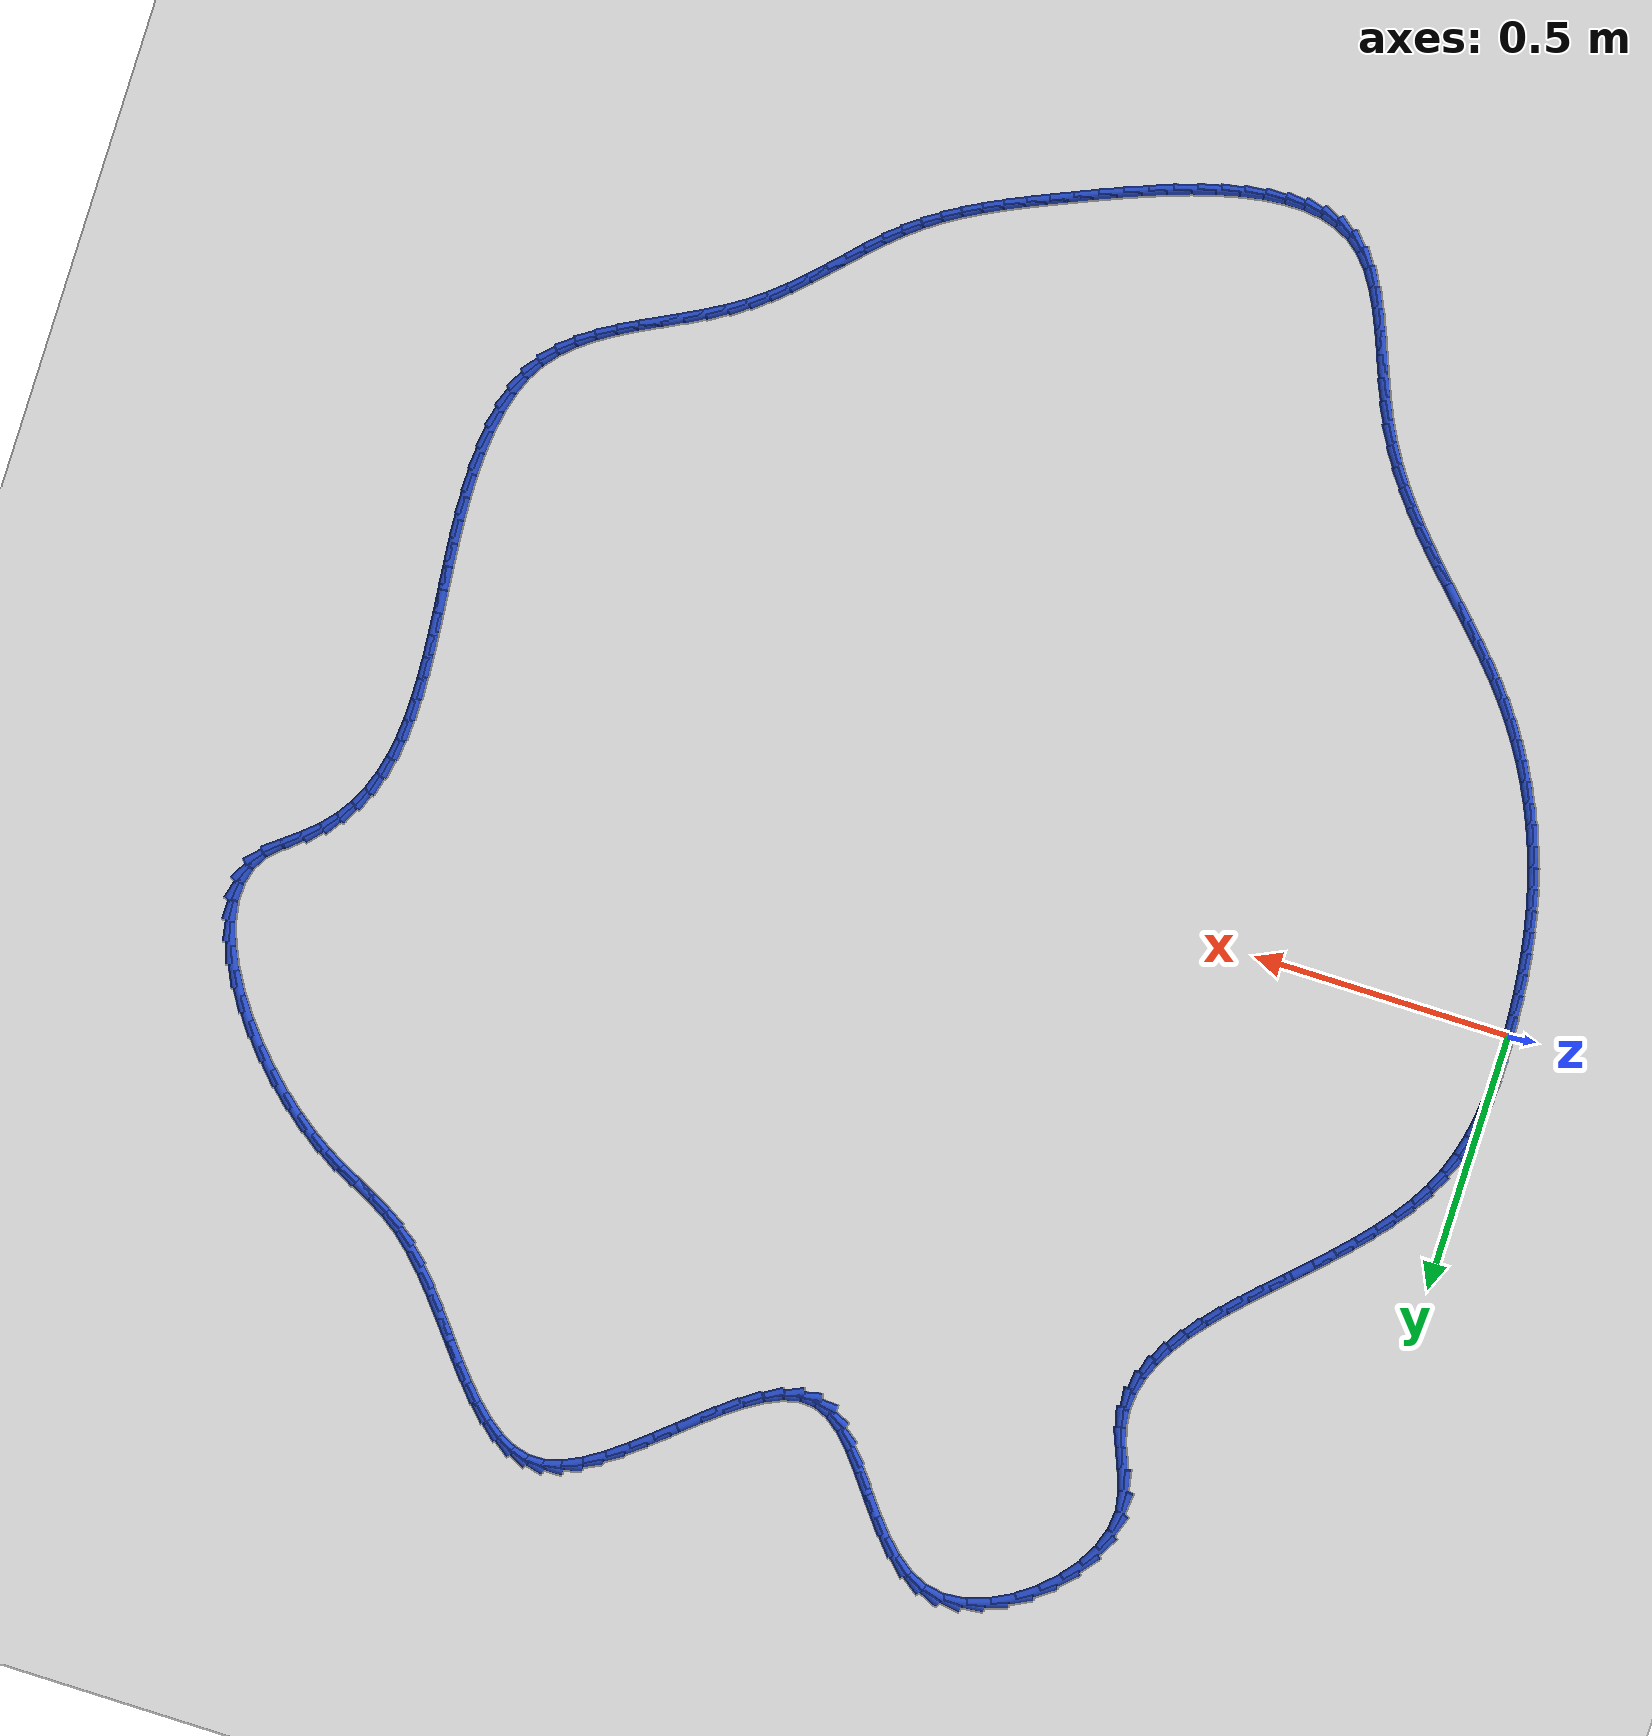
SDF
<sdf version="1.6">
 <world name="default">
  <light name="sun" type="directional">
   <pose>0 0 10 0 -0 0</pose>
   <diffuse>0.8 0.8 0.8 1</diffuse>
   <specular>0.2 0.2 0.2 1</specular>
   <attenuation>
    <range>1000</range>
    <constant>0.9</constant>
    <linear>0.01</linear>
    <quadratic>0.001</quadratic>
   </attenuation>
   <direction>-0.5 0.1 -0.9</direction>
  </light>
  <model name="ground_plane">
   <static>1</static>
   <link name="link">
    <collision name="collision">
     <geometry><plane><normal>0 0 1</normal><size>100 100</size></plane></geometry>
     <surface><friction><ode><mu>100</mu><mu2>50</mu2></ode></friction></surface>
    </collision>
    <visual name="visual">
     <cast_shadows>0</cast_shadows>
     <geometry><plane><normal>0 0 1</normal><size>100 100</size></plane></geometry>
     <material>
      <script><uri>file://media/materials/scripts/gazebo.material</uri><name>Gazebo/WhiteGlow</name></script>
     </material>
    </visual>
   </link>
  </model>
  <gravity>0 0 -9.8</gravity>
  <magnetic_field>6e-06 2.3e-05 -4.2e-05</magnetic_field>
  <atmosphere type="adiabatic"/>
  <physics name="default_physics" default="0" type="ode">
   <max_step_size>0.001</max_step_size>
   <real_time_factor>1</real_time_factor>
   <real_time_update_rate>1000</real_time_update_rate>
  </physics>
  <scene><ambient>0.4 0.4 0.4 1</ambient><background>0.7 0.7 0.7 1</background><shadows>1</shadows></scene>
  <spherical_coordinates>
   <surface_model>EARTH_WGS84</surface_model>
   <latitude_deg>0</latitude_deg>
   <longitude_deg>0</longitude_deg>
   <elevation>0</elevation>
   <heading_deg>0</heading_deg>
  </spherical_coordinates>
  <model name="line">
   <link name="link_0">
    <pose>5.421010862427522e-18 -2.0816681711721685e-17 0.01 0 1.57 -1.5428339865353886</pose>
    <collision name="collision">
     <geometry><cylinder><radius>0.01</radius><length>0.08</length></cylinder></geometry>
    </collision>
    <visual name="visual">
     <material>
      <script><name>Gazebo/Blue</name><uri>file://media/materials/scripts/gazebo.material</uri></script>
     </material>
     <geometry><cylinder><radius>0.01</radius><length>0.08</length></cylinder></geometry>
    </visual>
   </link>
   <link name="link_1">
    <pose>-0.0011414737055418522 0.040811183048679804 0.01 0 1.57 1.565398914404202</pose>
    <collision name="collision">
     <geometry><cylinder><radius>0.01</radius><length>0.08</length></cylinder></geometry>
    </collision>
    <visual name="visual">
     <material>
      <script><name>Gazebo/Blue</name><uri>file://media/materials/scripts/gazebo.material</uri></script>
     </material>
     <geometry><cylinder><radius>0.01</radius><length>0.08</length></cylinder></geometry>
    </visual>
   </link>
   <link name="link_2">
    <pose>-0.0009211176221651361 0.08163703210619166 0.01 0 1.57 1.5211755405178442</pose>
    <collision name="collision">
     <geometry><cylinder><radius>0.01</radius><length>0.08</length></cylinder></geometry>
    </collision>
    <visual name="visual">
     <material>
      <script><name>Gazebo/Blue</name><uri>file://media/materials/scripts/gazebo.material</uri></script>
     </material>
     <geometry><cylinder><radius>0.01</radius><length>0.08</length></cylinder></geometry>
    </visual>
   </link>
   <link name="link_3">
    <pose>0.0010990882258941938 0.12231650661455905 0.01 0 1.57 1.465713972385653</pose>
    <collision name="collision">
     <geometry><cylinder><radius>0.01</radius><length>0.08</length></cylinder></geometry>
    </collision>
    <visual name="visual">
     <material>
      <script><name>Gazebo/Blue</name><uri>file://media/materials/scripts/gazebo.material</uri></script>
     </material>
     <geometry><cylinder><radius>0.01</radius><length>0.08</length></cylinder></geometry>
    </visual>
   </link>
   <link name="link_4">
    <pose>0.005357163814400184 0.1626885660158054 0.01 0 1.57 1.398746401001696</pose>
    <collision name="collision">
     <geometry><cylinder><radius>0.01</radius><length>0.08</length></cylinder></geometry>
    </collision>
    <visual name="visual">
     <material>
      <script><name>Gazebo/Blue</name><uri>file://media/materials/scripts/gazebo.material</uri></script>
     </material>
     <geometry><cylinder><radius>0.01</radius><length>0.08</length></cylinder></geometry>
    </visual>
   </link>
   <link name="link_5">
    <pose>0.012291129119116874 0.20259216975195415 0.01 0 1.57 1.3203290934087182</pose>
    <collision name="collision">
     <geometry><cylinder><radius>0.01</radius><length>0.08</length></cylinder></geometry>
    </collision>
    <visual name="visual">
     <material>
      <script><name>Gazebo/Blue</name><uri>file://media/materials/scripts/gazebo.material</uri></script>
     </material>
     <geometry><cylinder><radius>0.01</radius><length>0.08</length></cylinder></geometry>
    </visual>
   </link>
   <link name="link_6">
    <pose>0.022339004115808296 0.24186627726502868 0.01 0 1.57 1.2311024524189376</pose>
    <collision name="collision">
     <geometry><cylinder><radius>0.01</radius><length>0.08</length></cylinder></geometry>
    </collision>
    <visual name="visual">
     <material>
      <script><name>Gazebo/Blue</name><uri>file://media/materials/scripts/gazebo.material</uri></script>
     </material>
     <geometry><cylinder><radius>0.01</radius><length>0.08</length></cylinder></geometry>
    </visual>
   </link>
   <link name="link_7">
    <pose>0.03593880878023852 0.28034984799705265 0.01 0 1.57 1.1325924355763268</pose>
    <collision name="collision">
     <geometry><cylinder><radius>0.01</radius><length>0.08</length></cylinder></geometry>
    </collision>
    <visual name="visual">
     <material>
      <script><name>Gazebo/Blue</name><uri>file://media/materials/scripts/gazebo.material</uri></script>
     </material>
     <geometry><cylinder><radius>0.01</radius><length>0.08</length></cylinder></geometry>
    </visual>
   </link>
   <link name="link_8">
    <pose>0.05352614476346979 0.31788245410216465 0.01 0 1.57 1.0348267820632442</pose>
    <collision name="collision">
     <geometry><cylinder><radius>0.01</radius><length>0.08</length></cylinder></geometry>
    </collision>
    <visual name="visual">
     <material>
      <script><name>Gazebo/Blue</name><uri>file://media/materials/scripts/gazebo.material</uri></script>
     </material>
     <geometry><cylinder><radius>0.01</radius><length>0.08</length></cylinder></geometry>
    </visual>
   </link>
   <link name="link_9">
    <pose>0.07520842756066638 0.35438681770757396 0.01 0 1.57 0.953844433200665</pose>
    <collision name="collision">
     <geometry><cylinder><radius>0.01</radius><length>0.08</length></cylinder></geometry>
    </collision>
    <visual name="visual">
     <material>
      <script><name>Gazebo/Blue</name><uri>file://media/materials/scripts/gazebo.material</uri></script>
     </material>
     <geometry><cylinder><radius>0.01</radius><length>0.08</length></cylinder></geometry>
    </visual>
   </link>
   <link name="link_10">
    <pose>0.1004355990052654 0.38995223992709344 0.01 0 1.57 0.8898535858384609</pose>
    <collision name="collision">
     <geometry><cylinder><radius>0.01</radius><length>0.08</length></cylinder></geometry>
    </collision>
    <visual name="visual">
     <material>
      <script><name>Gazebo/Blue</name><uri>file://media/materials/scripts/gazebo.material</uri></script>
     </material>
     <geometry><cylinder><radius>0.01</radius><length>0.08</length></cylinder></geometry>
    </visual>
   </link>
   <link name="link_11">
    <pose>0.12857918034324045 0.4246878906886786 0.01 0 1.57 0.8409457394628888</pose>
    <collision name="collision">
     <geometry><cylinder><radius>0.01</radius><length>0.08</length></cylinder></geometry>
    </collision>
    <visual name="visual">
     <material>
      <script><name>Gazebo/Blue</name><uri>file://media/materials/scripts/gazebo.material</uri></script>
     </material>
     <geometry><cylinder><radius>0.01</radius><length>0.08</length></cylinder></geometry>
    </visual>
   </link>
   <link name="link_12">
    <pose>0.15901069282056537 0.45870293992028516 0.01 0 1.57 0.8054376384249018</pose>
    <collision name="collision">
     <geometry><cylinder><radius>0.01</radius><length>0.08</length></cylinder></geometry>
    </collision>
    <visual name="visual">
     <material>
      <script><name>Gazebo/Blue</name><uri>file://media/materials/scripts/gazebo.material</uri></script>
     </material>
     <geometry><cylinder><radius>0.01</radius><length>0.08</length></cylinder></geometry>
    </visual>
   </link>
   <link name="link_13">
    <pose>0.19110165768321397 0.4921065575498688 0.01 0 1.57 0.7820571953414078</pose>
    <collision name="collision">
     <geometry><cylinder><radius>0.01</radius><length>0.08</length></cylinder></geometry>
    </collision>
    <visual name="visual">
     <material>
      <script><name>Gazebo/Blue</name><uri>file://media/materials/scripts/gazebo.material</uri></script>
     </material>
     <geometry><cylinder><radius>0.01</radius><length>0.08</length></cylinder></geometry>
    </visual>
   </link>
   <link name="link_14">
    <pose>0.22422359617715992 0.5250079135053849 0.01 0 1.57 0.7700104994845323</pose>
    <collision name="collision">
     <geometry><cylinder><radius>0.01</radius><length>0.08</length></cylinder></geometry>
    </collision>
    <visual name="visual">
     <material>
      <script><name>Gazebo/Blue</name><uri>file://media/materials/scripts/gazebo.material</uri></script>
     </material>
     <geometry><cylinder><radius>0.01</radius><length>0.08</length></cylinder></geometry>
    </visual>
   </link>
   <link name="link_15">
    <pose>0.25774802954837694 0.5575161777147893 0.01 0 1.57 0.769006754024356</pose>
    <collision name="collision">
     <geometry><cylinder><radius>0.01</radius><length>0.08</length></cylinder></geometry>
    </collision>
    <visual name="visual">
     <material>
      <script><name>Gazebo/Blue</name><uri>file://media/materials/scripts/gazebo.material</uri></script>
     </material>
     <geometry><cylinder><radius>0.01</radius><length>0.08</length></cylinder></geometry>
    </visual>
   </link>
   <link name="link_16">
    <pose>0.29104647904283876 0.5897405201060375 0.01 0 1.57 0.7792829584035748</pose>
    <collision name="collision">
     <geometry><cylinder><radius>0.01</radius><length>0.08</length></cylinder></geometry>
    </collision>
    <visual name="visual">
     <material>
      <script><name>Gazebo/Blue</name><uri>file://media/materials/scripts/gazebo.material</uri></script>
     </material>
     <geometry><cylinder><radius>0.01</radius><length>0.08</length></cylinder></geometry>
    </visual>
   </link>
   <link name="link_17">
    <pose>0.3234904659065193 0.6217901106070853 0.01 0 1.57 0.8016484157715186</pose>
    <collision name="collision">
     <geometry><cylinder><radius>0.01</radius><length>0.08</length></cylinder></geometry>
    </collision>
    <visual name="visual">
     <material>
      <script><name>Gazebo/Blue</name><uri>file://media/materials/scripts/gazebo.material</uri></script>
     </material>
     <geometry><cylinder><radius>0.01</radius><length>0.08</length></cylinder></geometry>
    </visual>
   </link>
   <link name="link_18">
    <pose>0.35445151138539205 0.6537741191458879 0.01 0 1.57 0.8375537802983192</pose>
    <collision name="collision">
     <geometry><cylinder><radius>0.01</radius><length>0.08</length></cylinder></geometry>
    </collision>
    <visual name="visual">
     <material>
      <script><name>Gazebo/Blue</name><uri>file://media/materials/scripts/gazebo.material</uri></script>
     </material>
     <geometry><cylinder><radius>0.01</radius><length>0.08</length></cylinder></geometry>
    </visual>
   </link>
   <link name="link_19">
    <pose>0.3833011367254309 0.685801715650401 0.01 0 1.57 0.8891691966846835</pose>
    <collision name="collision">
     <geometry><cylinder><radius>0.01</radius><length>0.08</length></cylinder></geometry>
    </collision>
    <visual name="visual">
     <material>
      <script><name>Gazebo/Blue</name><uri>file://media/materials/scripts/gazebo.material</uri></script>
     </material>
     <geometry><cylinder><radius>0.01</radius><length>0.08</length></cylinder></geometry>
    </visual>
   </link>
   <link name="link_20">
    <pose>0.4094108631726099 0.7179820700485811 0.01 0 1.57 0.9594138190496606</pose>
    <collision name="collision">
     <geometry><cylinder><radius>0.01</radius><length>0.08</length></cylinder></geometry>
    </collision>
    <visual name="visual">
     <material>
      <script><name>Gazebo/Blue</name><uri>file://media/materials/scripts/gazebo.material</uri></script>
     </material>
     <geometry><cylinder><radius>0.01</radius><length>0.08</length></cylinder></geometry>
    </visual>
   </link>
   <link name="link_21">
    <pose>0.4321522119729021 0.7504243522683824 0.01 0 1.57 1.051788305752772</pose>
    <collision name="collision">
     <geometry><cylinder><radius>0.01</radius><length>0.08</length></cylinder></geometry>
    </collision>
    <visual name="visual">
     <material>
      <script><name>Gazebo/Blue</name><uri>file://media/materials/scripts/gazebo.material</uri></script>
     </material>
     <geometry><cylinder><radius>0.01</radius><length>0.08</length></cylinder></geometry>
    </visual>
   </link>
   <link name="link_22">
    <pose>0.4508967043722817 0.7832377322377613 0.01 0 1.57 1.1697055127524718</pose>
    <collision name="collision">
     <geometry><cylinder><radius>0.01</radius><length>0.08</length></cylinder></geometry>
    </collision>
    <visual name="visual">
     <material>
      <script><name>Gazebo/Blue</name><uri>file://media/materials/scripts/gazebo.material</uri></script>
     </material>
     <geometry><cylinder><radius>0.01</radius><length>0.08</length></cylinder></geometry>
    </visual>
   </link>
   <link name="link_23">
    <pose>0.4650158616167225 0.8165313798846735 0.01 0 1.57 1.3148879507058695</pose>
    <collision name="collision">
     <geometry><cylinder><radius>0.01</radius><length>0.08</length></cylinder></geometry>
    </collision>
    <visual name="visual">
     <material>
      <script><name>Gazebo/Blue</name><uri>file://media/materials/scripts/gazebo.material</uri></script>
     </material>
     <geometry><cylinder><radius>0.01</radius><length>0.08</length></cylinder></geometry>
    </visual>
   </link>
   <link name="link_24">
    <pose>0.47388120495219804 0.850414465137074 0.01 0 1.57 1.4847483524341716</pose>
    <collision name="collision">
     <geometry><cylinder><radius>0.01</radius><length>0.08</length></cylinder></geometry>
    </collision>
    <visual name="visual">
     <material>
      <script><name>Gazebo/Blue</name><uri>file://media/materials/scripts/gazebo.material</uri></script>
     </material>
     <geometry><cylinder><radius>0.01</radius><length>0.08</length></cylinder></geometry>
    </visual>
   </link>
   <link name="link_25">
    <pose>0.47686425562468227 0.8849961579229191 0.01 0 1.57 -1.4714417642738244</pose>
    <collision name="collision">
     <geometry><cylinder><radius>0.01</radius><length>0.08</length></cylinder></geometry>
    </collision>
    <visual name="visual">
     <material>
      <script><name>Gazebo/Blue</name><uri>file://media/materials/scripts/gazebo.material</uri></script>
     </material>
     <geometry><cylinder><radius>0.01</radius><length>0.08</length></cylinder></geometry>
    </visual>
   </link>
   <link name="link_26">
    <pose>0.4733365348801487 0.920385628170164 0.01 0 1.57 -1.287138561494419</pose>
    <collision name="collision">
     <geometry><cylinder><radius>0.01</radius><length>0.08</length></cylinder></geometry>
    </collision>
    <visual name="visual">
     <material>
      <script><name>Gazebo/Blue</name><uri>file://media/materials/scripts/gazebo.material</uri></script>
     </material>
     <geometry><cylinder><radius>0.01</radius><length>0.08</length></cylinder></geometry>
    </visual>
   </link>
   <link name="link_27">
    <pose>0.46275240512069327 0.9566924883215487 0.01 0 1.57 -1.181320694218776</pose>
    <collision name="collision">
     <geometry><cylinder><radius>0.01</radius><length>0.08</length></cylinder></geometry>
    </collision>
    <visual name="visual">
     <material>
      <script><name>Gazebo/Blue</name><uri>file://media/materials/scripts/gazebo.material</uri></script>
     </material>
     <geometry><cylinder><radius>0.01</radius><length>0.08</length></cylinder></geometry>
    </visual>
   </link>
   <link name="link_28">
    <pose>0.44742275411991567 0.9940416095965813 0.01 0 1.57 -1.2165671565249727</pose>
    <collision name="collision">
     <geometry><cylinder><radius>0.01</radius><length>0.08</length></cylinder></geometry>
    </collision>
    <visual name="visual">
     <material>
      <script><name>Gazebo/Blue</name><uri>file://media/materials/scripts/gazebo.material</uri></script>
     </material>
     <geometry><cylinder><radius>0.01</radius><length>0.08</length></cylinder></geometry>
    </visual>
   </link>
   <link name="link_29">
    <pose>0.43317140119592945 1.0325766283336713 0.01 0 1.57 -1.3935668420942937</pose>
    <collision name="collision">
     <geometry><cylinder><radius>0.01</radius><length>0.08</length></cylinder></geometry>
    </collision>
    <visual name="visual">
     <material>
      <script><name>Gazebo/Blue</name><uri>file://media/materials/scripts/gazebo.material</uri></script>
     </material>
     <geometry><cylinder><radius>0.01</radius><length>0.08</length></cylinder></geometry>
    </visual>
   </link>
   <link name="link_30">
    <pose>0.42603133349606975 1.0724410645441176 0.01 0 1.57 1.4740837462692427</pose>
    <collision name="collision">
     <geometry><cylinder><radius>0.01</radius><length>0.08</length></cylinder></geometry>
    </collision>
    <visual name="visual">
     <material>
      <script><name>Gazebo/Blue</name><uri>file://media/materials/scripts/gazebo.material</uri></script>
     </material>
     <geometry><cylinder><radius>0.01</radius><length>0.08</length></cylinder></geometry>
    </visual>
   </link>
   <link name="link_31">
    <pose>0.4300044510954093 1.1133946050493109 0.01 0 1.57 1.2361715861931493</pose>
    <collision name="collision">
     <geometry><cylinder><radius>0.01</radius><length>0.08</length></cylinder></geometry>
    </collision>
    <visual name="visual">
     <material>
      <script><name>Gazebo/Blue</name><uri>file://media/materials/scripts/gazebo.material</uri></script>
     </material>
     <geometry><cylinder><radius>0.01</radius><length>0.08</length></cylinder></geometry>
    </visual>
   </link>
   <link name="link_32">
    <pose>0.4442188941877277 1.1542758974756078 0.01 0 1.57 1.0461454764134763</pose>
    <collision name="collision">
     <geometry><cylinder><radius>0.01</radius><length>0.08</length></cylinder></geometry>
    </collision>
    <visual name="visual">
     <material>
      <script><name>Gazebo/Blue</name><uri>file://media/materials/scripts/gazebo.material</uri></script>
     </material>
     <geometry><cylinder><radius>0.01</radius><length>0.08</length></cylinder></geometry>
    </visual>
   </link>
   <link name="link_33">
    <pose>0.4670868439036568 1.193788288085476 0.01 0 1.57 0.8885519668398391</pose>
    <collision name="collision">
     <geometry><cylinder><radius>0.01</radius><length>0.08</length></cylinder></geometry>
    </collision>
    <visual name="visual">
     <material>
      <script><name>Gazebo/Blue</name><uri>file://media/materials/scripts/gazebo.material</uri></script>
     </material>
     <geometry><cylinder><radius>0.01</radius><length>0.08</length></cylinder></geometry>
    </visual>
   </link>
   <link name="link_34">
    <pose>0.49702048137382837 1.2306351231413855 0.01 0 1.57 0.7484161495095302</pose>
    <collision name="collision">
     <geometry><cylinder><radius>0.01</radius><length>0.08</length></cylinder></geometry>
    </collision>
    <visual name="visual">
     <material>
      <script><name>Gazebo/Blue</name><uri>file://media/materials/scripts/gazebo.material</uri></script>
     </material>
     <geometry><cylinder><radius>0.01</radius><length>0.08</length></cylinder></geometry>
    </visual>
   </link>
   <link name="link_35">
    <pose>0.5324319877288745 1.2635197489058037 0.01 0 1.57 0.6126815225585893</pose>
    <collision name="collision">
     <geometry><cylinder><radius>0.01</radius><length>0.08</length></cylinder></geometry>
    </collision>
    <visual name="visual">
     <material>
      <script><name>Gazebo/Blue</name><uri>file://media/materials/scripts/gazebo.material</uri></script>
     </material>
     <geometry><cylinder><radius>0.01</radius><length>0.08</length></cylinder></geometry>
    </visual>
   </link>
   <link name="link_36">
    <pose>0.5717335440994264 1.2911455116411998 0.01 0 1.57 0.4687944338650248</pose>
    <collision name="collision">
     <geometry><cylinder><radius>0.01</radius><length>0.08</length></cylinder></geometry>
    </collision>
    <visual name="visual">
     <material>
      <script><name>Gazebo/Blue</name><uri>file://media/materials/scripts/gazebo.material</uri></script>
     </material>
     <geometry><cylinder><radius>0.01</radius><length>0.08</length></cylinder></geometry>
    </visual>
   </link>
   <link name="link_37">
    <pose>0.6133373316161166 1.3122157576100422 0.01 0 1.57 0.30274790113291394</pose>
    <collision name="collision">
     <geometry><cylinder><radius>0.01</radius><length>0.08</length></cylinder></geometry>
    </collision>
    <visual name="visual">
     <material>
      <script><name>Gazebo/Blue</name><uri>file://media/materials/scripts/gazebo.material</uri></script>
     </material>
     <geometry><cylinder><radius>0.01</radius><length>0.08</length></cylinder></geometry>
    </visual>
   </link>
   <link name="link_38">
    <pose>0.6556555314095769 1.3254338330748 0.01 0 1.57 0.09787116318990208</pose>
    <collision name="collision">
     <geometry><cylinder><radius>0.01</radius><length>0.08</length></cylinder></geometry>
    </collision>
    <visual name="visual">
     <material>
      <script><name>Gazebo/Blue</name><uri>file://media/materials/scripts/gazebo.material</uri></script>
     </material>
     <geometry><cylinder><radius>0.01</radius><length>0.08</length></cylinder></geometry>
    </visual>
   </link>
   <link name="link_39">
    <pose>0.6971003246104387 1.329503084297941 0.01 0 1.57 -0.16102958598154918</pose>
    <collision name="collision">
     <geometry><cylinder><radius>0.01</radius><length>0.08</length></cylinder></geometry>
    </collision>
    <visual name="visual">
     <material>
      <script><name>Gazebo/Blue</name><uri>file://media/materials/scripts/gazebo.material</uri></script>
     </material>
     <geometry><cylinder><radius>0.01</radius><length>0.08</length></cylinder></geometry>
    </visual>
   </link>
   <link name="link_40">
    <pose>0.7361080149091528 1.3231668296931003 0.01 0 1.57 -0.43189429138741975</pose>
    <collision name="collision">
     <geometry><cylinder><radius>0.01</radius><length>0.08</length></cylinder></geometry>
    </collision>
    <visual name="visual">
     <material>
      <script><name>Gazebo/Blue</name><uri>file://media/materials/scripts/gazebo.material</uri></script>
     </material>
     <geometry><cylinder><radius>0.01</radius><length>0.08</length></cylinder></geometry>
    </visual>
   </link>
   <link name="link_41">
    <pose>0.7719946273835748 1.3066261250179432 0.01 0 1.57 -0.6398349906789519</pose>
    <collision name="collision">
     <geometry><cylinder><radius>0.01</radius><length>0.08</length></cylinder></geometry>
    </collision>
    <visual name="visual">
     <material>
      <script><name>Gazebo/Blue</name><uri>file://media/materials/scripts/gazebo.material</uri></script>
     </material>
     <geometry><cylinder><radius>0.01</radius><length>0.08</length></cylinder></geometry>
    </visual>
   </link>
   <link name="link_42">
    <pose>0.8051864873626604 1.2819218427747143 0.01 0 1.57 -0.7807768083004512</pose>
    <collision name="collision">
     <geometry><cylinder><radius>0.01</radius><length>0.08</length></cylinder></geometry>
    </collision>
    <visual name="visual">
     <material>
      <script><name>Gazebo/Blue</name><uri>file://media/materials/scripts/gazebo.material</uri></script>
     </material>
     <geometry><cylinder><radius>0.01</radius><length>0.08</length></cylinder></geometry>
    </visual>
   </link>
   <link name="link_43">
    <pose>0.8361809432612242 1.2512125438679522 0.01 0 1.57 -0.8676140089708787</pose>
    <collision name="collision">
     <geometry><cylinder><radius>0.01</radius><length>0.08</length></cylinder></geometry>
    </collision>
    <visual name="visual">
     <material>
      <script><name>Gazebo/Blue</name><uri>file://media/materials/scripts/gazebo.material</uri></script>
     </material>
     <geometry><cylinder><radius>0.01</radius><length>0.08</length></cylinder></geometry>
    </visual>
   </link>
   <link name="link_44">
    <pose>0.865475343494082 1.2166567892021953 0.01 0 1.57 -0.9114368812657686</pose>
    <collision name="collision">
     <geometry><cylinder><radius>0.01</radius><length>0.08</length></cylinder></geometry>
    </collision>
    <visual name="visual">
     <material>
      <script><name>Gazebo/Blue</name><uri>file://media/materials/scripts/gazebo.material</uri></script>
     </material>
     <geometry><cylinder><radius>0.01</radius><length>0.08</length></cylinder></geometry>
    </visual>
   </link>
   <link name="link_45">
    <pose>0.8935670364760493 1.1804131396819828 0.01 0 1.57 -0.9174115135770619</pose>
    <collision name="collision">
     <geometry><cylinder><radius>0.01</radius><length>0.08</length></cylinder></geometry>
    </collision>
    <visual name="visual">
     <material>
      <script><name>Gazebo/Blue</name><uri>file://media/materials/scripts/gazebo.material</uri></script>
     </material>
     <geometry><cylinder><radius>0.01</radius><length>0.08</length></cylinder></geometry>
    </visual>
   </link>
   <link name="link_46">
    <pose>0.9209533706219416 1.1446401562118524 0.01 0 1.57 -0.883970678081547</pose>
    <collision name="collision">
     <geometry><cylinder><radius>0.01</radius><length>0.08</length></cylinder></geometry>
    </collision>
    <visual name="visual">
     <material>
      <script><name>Gazebo/Blue</name><uri>file://media/materials/scripts/gazebo.material</uri></script>
     </material>
     <geometry><cylinder><radius>0.01</radius><length>0.08</length></cylinder></geometry>
    </visual>
   </link>
   <link name="link_47">
    <pose>0.9481316943465741 1.1114963996963434 0.01 0 1.57 -0.8013095608818674</pose>
    <collision name="collision">
     <geometry><cylinder><radius>0.01</radius><length>0.08</length></cylinder></geometry>
    </collision>
    <visual name="visual">
     <material>
      <script><name>Gazebo/Blue</name><uri>file://media/materials/scripts/gazebo.material</uri></script>
     </material>
     <geometry><cylinder><radius>0.01</radius><length>0.08</length></cylinder></geometry>
    </visual>
   </link>
   <link name="link_48">
    <pose>0.9755993560647622 1.083140431039994 0.01 0 1.57 -0.6484401586271312</pose>
    <collision name="collision">
     <geometry><cylinder><radius>0.01</radius><length>0.08</length></cylinder></geometry>
    </collision>
    <visual name="visual">
     <material>
      <script><name>Gazebo/Blue</name><uri>file://media/materials/scripts/gazebo.material</uri></script>
     </material>
     <geometry><cylinder><radius>0.01</radius><length>0.08</length></cylinder></geometry>
    </visual>
   </link>
   <link name="link_49">
    <pose>1.0038537041913216 1.061730811147342 0.01 0 1.57 -0.394727970321053</pose>
    <collision name="collision">
     <geometry><cylinder><radius>0.01</radius><length>0.08</length></cylinder></geometry>
    </collision>
    <visual name="visual">
     <material>
      <script><name>Gazebo/Blue</name><uri>file://media/materials/scripts/gazebo.material</uri></script>
     </material>
     <geometry><cylinder><radius>0.01</radius><length>0.08</length></cylinder></geometry>
    </visual>
   </link>
   <link name="link_50">
    <pose>1.0333919495292925 1.0494253980280288 0.01 0 1.57 -0.059929105691222534</pose>
    <collision name="collision">
     <geometry><cylinder><radius>0.01</radius><length>0.08</length></cylinder></geometry>
    </collision>
    <visual name="visual">
     <material>
      <script><name>Gazebo/Blue</name><uri>file://media/materials/scripts/gazebo.material</uri></script>
     </material>
     <geometry><cylinder><radius>0.01</radius><length>0.08</length></cylinder></geometry>
    </visual>
   </link>
   <link name="link_51">
    <pose>1.0645495627103858 1.0475559115130457 0.01 0 1.57 0.22516677115780626</pose>
    <collision name="collision">
     <geometry><cylinder><radius>0.01</radius><length>0.08</length></cylinder></geometry>
    </collision>
    <visual name="visual">
     <material>
      <script><name>Gazebo/Blue</name><uri>file://media/materials/scripts/gazebo.material</uri></script>
     </material>
     <geometry><cylinder><radius>0.01</radius><length>0.08</length></cylinder></geometry>
    </visual>
   </link>
   <link name="link_52">
    <pose>1.0971877701576767 1.0550317217874212 0.01 0 1.57 0.4237539195885437</pose>
    <collision name="collision">
     <geometry><cylinder><radius>0.01</radius><length>0.08</length></cylinder></geometry>
    </collision>
    <visual name="visual">
     <material>
      <script><name>Gazebo/Blue</name><uri>file://media/materials/scripts/gazebo.material</uri></script>
     </material>
     <geometry><cylinder><radius>0.01</radius><length>0.08</length></cylinder></geometry>
    </visual>
   </link>
   <link name="link_53">
    <pose>1.1310813266219522 1.0703205181027404 0.01 0 1.57 0.5532730920960734</pose>
    <collision name="collision">
     <geometry><cylinder><radius>0.01</radius><length>0.08</length></cylinder></geometry>
    </collision>
    <visual name="visual">
     <material>
      <script><name>Gazebo/Blue</name><uri>file://media/materials/scripts/gazebo.material</uri></script>
     </material>
     <geometry><cylinder><radius>0.01</radius><length>0.08</length></cylinder></geometry>
    </visual>
   </link>
   <link name="link_54">
    <pose>1.1660049868540003 1.0918899897105898 0.01 0 1.57 0.6348736017017773</pose>
    <collision name="collision">
     <geometry><cylinder><radius>0.01</radius><length>0.08</length></cylinder></geometry>
    </collision>
    <visual name="visual">
     <material>
      <script><name>Gazebo/Blue</name><uri>file://media/materials/scripts/gazebo.material</uri></script>
     </material>
     <geometry><cylinder><radius>0.01</radius><length>0.08</length></cylinder></geometry>
    </visual>
   </link>
   <link name="link_55">
    <pose>1.2017335056046081 1.1182078258625547 0.01 0 1.57 0.6828726116170073</pose>
    <collision name="collision">
     <geometry><cylinder><radius>0.01</radius><length>0.08</length></cylinder></geometry>
    </collision>
    <visual name="visual">
     <material>
      <script><name>Gazebo/Blue</name><uri>file://media/materials/scripts/gazebo.material</uri></script>
     </material>
     <geometry><cylinder><radius>0.01</radius><length>0.08</length></cylinder></geometry>
    </visual>
   </link>
   <link name="link_56">
    <pose>1.2380416376245642 1.147741715810221 0.01 0 1.57 0.7053565660442894</pose>
    <collision name="collision">
     <geometry><cylinder><radius>0.01</radius><length>0.08</length></cylinder></geometry>
    </collision>
    <visual name="visual">
     <material>
      <script><name>Gazebo/Blue</name><uri>file://media/materials/scripts/gazebo.material</uri></script>
     </material>
     <geometry><cylinder><radius>0.01</radius><length>0.08</length></cylinder></geometry>
    </visual>
   </link>
   <link name="link_57">
    <pose>1.274704137664656 1.1789593488051757 0.01 0 1.57 0.706009868089719</pose>
    <collision name="collision">
     <geometry><cylinder><radius>0.01</radius><length>0.08</length></cylinder></geometry>
    </collision>
    <visual name="visual">
     <material>
      <script><name>Gazebo/Blue</name><uri>file://media/materials/scripts/gazebo.material</uri></script>
     </material>
     <geometry><cylinder><radius>0.01</radius><length>0.08</length></cylinder></geometry>
    </visual>
   </link>
   <link name="link_58">
    <pose>1.3114957604756703 1.2103284140990034 0.01 0 1.57 0.6851513043498499</pose>
    <collision name="collision">
     <geometry><cylinder><radius>0.01</radius><length>0.08</length></cylinder></geometry>
    </collision>
    <visual name="visual">
     <material>
      <script><name>Gazebo/Blue</name><uri>file://media/materials/scripts/gazebo.material</uri></script>
     </material>
     <geometry><cylinder><radius>0.01</radius><length>0.08</length></cylinder></geometry>
    </visual>
   </link>
   <link name="link_59">
    <pose>1.3481912608083955 1.2403166009432907 0.01 0 1.57 0.6398737353921345</pose>
    <collision name="collision">
     <geometry><cylinder><radius>0.01</radius><length>0.08</length></cylinder></geometry>
    </collision>
    <visual name="visual">
     <material>
      <script><name>Gazebo/Blue</name><uri>file://media/materials/scripts/gazebo.material</uri></script>
     </material>
     <geometry><cylinder><radius>0.01</radius><length>0.08</length></cylinder></geometry>
    </visual>
   </link>
   <link name="link_60">
    <pose>1.3845653934136193 1.2673915985896234 0.01 0 1.57 0.5633479967560674</pose>
    <collision name="collision">
     <geometry><cylinder><radius>0.01</radius><length>0.08</length></cylinder></geometry>
    </collision>
    <visual name="visual">
     <material>
      <script><name>Gazebo/Blue</name><uri>file://media/materials/scripts/gazebo.material</uri></script>
     </material>
     <geometry><cylinder><radius>0.01</radius><length>0.08</length></cylinder></geometry>
    </visual>
   </link>
   <link name="link_61">
    <pose>1.4203929130421298 1.2900210962895875 0.01 0 1.57 0.443454104782981</pose>
    <collision name="collision">
     <geometry><cylinder><radius>0.01</radius><length>0.08</length></cylinder></geometry>
    </collision>
    <visual name="visual">
     <material>
      <script><name>Gazebo/Blue</name><uri>file://media/materials/scripts/gazebo.material</uri></script>
     </material>
     <geometry><cylinder><radius>0.01</radius><length>0.08</length></cylinder></geometry>
    </visual>
   </link>
   <link name="link_62">
    <pose>1.455448574444714 1.3066727832947689 0.01 0 1.57 0.2622267586462871</pose>
    <collision name="collision">
     <geometry><cylinder><radius>0.01</radius><length>0.08</length></cylinder></geometry>
    </collision>
    <visual name="visual">
     <material>
      <script><name>Gazebo/Blue</name><uri>file://media/materials/scripts/gazebo.material</uri></script>
     </material>
     <geometry><cylinder><radius>0.01</radius><length>0.08</length></cylinder></geometry>
    </visual>
   </link>
   <link name="link_63">
    <pose>1.4895071323721594 1.3158143488567529 0.01 0 1.57 0.008959498481161295</pose>
    <collision name="collision">
     <geometry><cylinder><radius>0.01</radius><length>0.08</length></cylinder></geometry>
    </collision>
    <visual name="visual">
     <material>
      <script><name>Gazebo/Blue</name><uri>file://media/materials/scripts/gazebo.material</uri></script>
     </material>
     <geometry><cylinder><radius>0.01</radius><length>0.08</length></cylinder></geometry>
    </visual>
   </link>
   <link name="link_64">
    <pose>1.5223737825477859 1.3161088254385926 0.01 0 1.57 -0.2543006514144499</pose>
    <collision name="collision">
     <geometry><cylinder><radius>0.01</radius><length>0.08</length></cylinder></geometry>
    </collision>
    <visual name="visual">
     <material>
      <script><name>Gazebo/Blue</name><uri>file://media/materials/scripts/gazebo.material</uri></script>
     </material>
     <geometry><cylinder><radius>0.01</radius><length>0.08</length></cylinder></geometry>
    </visual>
   </link>
   <link name="link_65">
    <pose>1.554109381991304 1.307859853359536 0.01 0 1.57 -0.47069046316593033</pose>
    <collision name="collision">
     <geometry><cylinder><radius>0.01</radius><length>0.08</length></cylinder></geometry>
    </collision>
    <visual name="visual">
     <material>
      <script><name>Gazebo/Blue</name><uri>file://media/materials/scripts/gazebo.material</uri></script>
     </material>
     <geometry><cylinder><radius>0.01</radius><length>0.08</length></cylinder></geometry>
    </visual>
   </link>
   <link name="link_66">
    <pose>1.5849025902804927 1.2921911966093431 0.01 0 1.57 -0.6312070473543551</pose>
    <collision name="collision">
     <geometry><cylinder><radius>0.01</radius><length>0.08</length></cylinder></geometry>
    </collision>
    <visual name="visual">
     <material>
      <script><name>Gazebo/Blue</name><uri>file://media/materials/scripts/gazebo.material</uri></script>
     </material>
     <geometry><cylinder><radius>0.01</radius><length>0.08</length></cylinder></geometry>
    </visual>
   </link>
   <link name="link_67">
    <pose>1.6149430139416245 1.270232695854855 0.01 0 1.57 -0.743745261661115</pose>
    <collision name="collision">
     <geometry><cylinder><radius>0.01</radius><length>0.08</length></cylinder></geometry>
    </collision>
    <visual name="visual">
     <material>
      <script><name>Gazebo/Blue</name><uri>file://media/materials/scripts/gazebo.material</uri></script>
     </material>
     <geometry><cylinder><radius>0.01</radius><length>0.08</length></cylinder></geometry>
    </visual>
   </link>
   <link name="link_68">
    <pose>1.6444202595009738 1.2431141917629158 0.01 0 1.57 -0.8193256100123941</pose>
    <collision name="collision">
     <geometry><cylinder><radius>0.01</radius><length>0.08</length></cylinder></geometry>
    </collision>
    <visual name="visual">
     <material>
      <script><name>Gazebo/Blue</name><uri>file://media/materials/scripts/gazebo.material</uri></script>
     </material>
     <geometry><cylinder><radius>0.01</radius><length>0.08</length></cylinder></geometry>
    </visual>
   </link>
   <link name="link_69">
    <pose>1.6735239334848124 1.211965525000367 0.01 0 1.57 -0.8666763242689905</pose>
    <collision name="collision">
     <geometry><cylinder><radius>0.01</radius><length>0.08</length></cylinder></geometry>
    </collision>
    <visual name="visual">
     <material>
      <script><name>Gazebo/Blue</name><uri>file://media/materials/scripts/gazebo.material</uri></script>
     </material>
     <geometry><cylinder><radius>0.01</radius><length>0.08</length></cylinder></geometry>
    </visual>
   </link>
   <link name="link_70">
    <pose>1.7024436424194154 1.1779165362340518 0.01 0 1.57 -0.8914798488127407</pose>
    <collision name="collision">
     <geometry><cylinder><radius>0.01</radius><length>0.08</length></cylinder></geometry>
    </collision>
    <visual name="visual">
     <material>
      <script><name>Gazebo/Blue</name><uri>file://media/materials/scripts/gazebo.material</uri></script>
     </material>
     <geometry><cylinder><radius>0.01</radius><length>0.08</length></cylinder></geometry>
    </visual>
   </link>
   <link name="link_71">
    <pose>1.7313689928310545 1.1420970661308125 0.01 0 1.57 -0.8968501118826236</pose>
    <collision name="collision">
     <geometry><cylinder><radius>0.01</radius><length>0.08</length></cylinder></geometry>
    </collision>
    <visual name="visual">
     <material>
      <script><name>Gazebo/Blue</name><uri>file://media/materials/scripts/gazebo.material</uri></script>
     </material>
     <geometry><cylinder><radius>0.01</radius><length>0.08</length></cylinder></geometry>
    </visual>
   </link>
   <link name="link_72">
    <pose>1.7604895912460041 1.1056369553574918 0.01 0 1.57 -0.8838240015843302</pose>
    <collision name="collision">
     <geometry><cylinder><radius>0.01</radius><length>0.08</length></cylinder></geometry>
    </collision>
    <visual name="visual">
     <material>
      <script><name>Gazebo/Blue</name><uri>file://media/materials/scripts/gazebo.material</uri></script>
     </material>
     <geometry><cylinder><radius>0.01</radius><length>0.08</length></cylinder></geometry>
    </visual>
   </link>
   <link name="link_73">
    <pose>1.7899950441905372 1.0696660445809327 0.01 0 1.57 -0.8516032647216885</pose>
    <collision name="collision">
     <geometry><cylinder><radius>0.01</radius><length>0.08</length></cylinder></geometry>
    </collision>
    <visual name="visual">
     <material>
      <script><name>Gazebo/Blue</name><uri>file://media/materials/scripts/gazebo.material</uri></script>
     </material>
     <geometry><cylinder><radius>0.01</radius><length>0.08</length></cylinder></geometry>
    </visual>
   </link>
   <link name="link_74">
    <pose>1.8200749581909266 1.0353141744679768 0.01 0 1.57 -0.7975519928433182</pose>
    <collision name="collision">
     <geometry><cylinder><radius>0.01</radius><length>0.08</length></cylinder></geometry>
    </collision>
    <visual name="visual">
     <material>
      <script><name>Gazebo/Blue</name><uri>file://media/materials/scripts/gazebo.material</uri></script>
     </material>
     <geometry><cylinder><radius>0.01</radius><length>0.08</length></cylinder></geometry>
    </visual>
   </link>
   <link name="link_75">
    <pose>1.850918939773446 1.0037111856854677 0.01 0 1.57 -0.7170695965001556</pose>
    <collision name="collision">
     <geometry><cylinder><radius>0.01</radius><length>0.08</length></cylinder></geometry>
    </collision>
    <visual name="visual">
     <material>
      <script><name>Gazebo/Blue</name><uri>file://media/materials/scripts/gazebo.material</uri></script>
     </material>
     <geometry><cylinder><radius>0.01</radius><length>0.08</length></cylinder></geometry>
    </visual>
   </link>
   <link name="link_76">
    <pose>1.8827165954643696 0.9759869189002478 0.01 0 1.57 -0.6087301896084494</pose>
    <collision name="collision">
     <geometry><cylinder><radius>0.01</radius><length>0.08</length></cylinder></geometry>
    </collision>
    <visual name="visual">
     <material>
      <script><name>Gazebo/Blue</name><uri>file://media/materials/scripts/gazebo.material</uri></script>
     </material>
     <geometry><cylinder><radius>0.01</radius><length>0.08</length></cylinder></geometry>
    </visual>
   </link>
   <link name="link_77">
    <pose>1.9156401284164857 0.9530382142325524 0.01 0 1.57 -0.5140570098459021</pose>
    <collision name="collision">
     <geometry><cylinder><radius>0.01</radius><length>0.08</length></cylinder></geometry>
    </collision>
    <visual name="visual">
     <material>
      <script><name>Gazebo/Blue</name><uri>file://media/materials/scripts/gazebo.material</uri></script>
     </material>
     <geometry><cylinder><radius>0.01</radius><length>0.08</length></cylinder></geometry>
    </visual>
   </link>
   <link name="link_78">
    <pose>1.949714923377538 0.9337962717121426 0.01 0 1.57 -0.46367861394394416</pose>
    <collision name="collision">
     <geometry><cylinder><radius>0.01</radius><length>0.08</length></cylinder></geometry>
    </collision>
    <visual name="visual">
     <material>
      <script><name>Gazebo/Blue</name><uri>file://media/materials/scripts/gazebo.material</uri></script>
     </material>
     <geometry><cylinder><radius>0.01</radius><length>0.08</length></cylinder></geometry>
    </visual>
   </link>
   <link name="link_79">
    <pose>1.9848926981749786 0.916206020936152 0.01 0 1.57 -0.4611069807576531</pose>
    <collision name="collision">
     <geometry><cylinder><radius>0.01</radius><length>0.08</length></cylinder></geometry>
    </collision>
    <visual name="visual">
     <material>
      <script><name>Gazebo/Blue</name><uri>file://media/materials/scripts/gazebo.material</uri></script>
     </material>
     <geometry><cylinder><radius>0.01</radius><length>0.08</length></cylinder></geometry>
    </visual>
   </link>
   <link name="link_80">
    <pose>2.021124617093376 0.8982049805365434 0.01 0 1.57 -0.5027161206493165</pose>
    <collision name="collision">
     <geometry><cylinder><radius>0.01</radius><length>0.08</length></cylinder></geometry>
    </collision>
    <visual name="visual">
     <material>
      <script><name>Gazebo/Blue</name><uri>file://media/materials/scripts/gazebo.material</uri></script>
     </material>
     <geometry><cylinder><radius>0.01</radius><length>0.08</length></cylinder></geometry>
    </visual>
   </link>
   <link name="link_81">
    <pose>2.058361844417296 0.877730669145279 0.01 0 1.57 -0.5746208051728079</pose>
    <collision name="collision">
     <geometry><cylinder><radius>0.01</radius><length>0.08</length></cylinder></geometry>
    </collision>
    <visual name="visual">
     <material>
      <script><name>Gazebo/Blue</name><uri>file://media/materials/scripts/gazebo.material</uri></script>
     </material>
     <geometry><cylinder><radius>0.01</radius><length>0.08</length></cylinder></geometry>
    </visual>
   </link>
   <link name="link_82">
    <pose>2.0964655608591576 0.8530582390028494 0.01 0 1.57 -0.6445030631017857</pose>
    <collision name="collision">
     <geometry><cylinder><radius>0.01</radius><length>0.08</length></cylinder></geometry>
    </collision>
    <visual name="visual">
     <material>
      <script><name>Gazebo/Blue</name><uri>file://media/materials/scripts/gazebo.material</uri></script>
     </material>
     <geometry><cylinder><radius>0.01</radius><length>0.08</length></cylinder></geometry>
    </visual>
   </link>
   <link name="link_83">
    <pose>2.134826702071948 0.8242272814858503 0.01 0 1.57 -0.7075148353340386</pose>
    <collision name="collision">
     <geometry><cylinder><radius>0.01</radius><length>0.08</length></cylinder></geometry>
    </collision>
    <visual name="visual">
     <material>
      <script><name>Gazebo/Blue</name><uri>file://media/materials/scripts/gazebo.material</uri></script>
     </material>
     <geometry><cylinder><radius>0.01</radius><length>0.08</length></cylinder></geometry>
    </visual>
   </link>
   <link name="link_84">
    <pose>2.1726831002842553 0.7918518579593881 0.01 0 1.57 -0.767542225457668</pose>
    <collision name="collision">
     <geometry><cylinder><radius>0.01</radius><length>0.08</length></cylinder></geometry>
    </collision>
    <visual name="visual">
     <material>
      <script><name>Gazebo/Blue</name><uri>file://media/materials/scripts/gazebo.material</uri></script>
     </material>
     <geometry><cylinder><radius>0.01</radius><length>0.08</length></cylinder></geometry>
    </visual>
   </link>
   <link name="link_85">
    <pose>2.2092725047235064 0.756546341222975 0.01 0 1.57 -0.8277808865502475</pose>
    <collision name="collision">
     <geometry><cylinder><radius>0.01</radius><length>0.08</length></cylinder></geometry>
    </collision>
    <visual name="visual">
     <material>
      <script><name>Gazebo/Blue</name><uri>file://media/materials/scripts/gazebo.material</uri></script>
     </material>
     <geometry><cylinder><radius>0.01</radius><length>0.08</length></cylinder></geometry>
    </visual>
   </link>
   <link name="link_86">
    <pose>2.243832664617129 0.7189251040761271 0.01 0 1.57 -0.8912576350863156</pose>
    <collision name="collision">
     <geometry><cylinder><radius>0.01</radius><length>0.08</length></cylinder></geometry>
    </collision>
    <visual name="visual">
     <material>
      <script><name>Gazebo/Blue</name><uri>file://media/materials/scripts/gazebo.material</uri></script>
     </material>
     <geometry><cylinder><radius>0.01</radius><length>0.08</length></cylinder></geometry>
    </visual>
   </link>
   <link name="link_87">
    <pose>2.275601329192552 0.6796025193183581 0.01 0 1.57 -0.9612634005826799</pose>
    <collision name="collision">
     <geometry><cylinder><radius>0.01</radius><length>0.08</length></cylinder></geometry>
    </collision>
    <visual name="visual">
     <material>
      <script><name>Gazebo/Blue</name><uri>file://media/materials/scripts/gazebo.material</uri></script>
     </material>
     <geometry><cylinder><radius>0.01</radius><length>0.08</length></cylinder></geometry>
    </visual>
   </link>
   <link name="link_88">
    <pose>2.3038162476772017 0.6391929597491826 0.01 0 1.57 -1.0417917243754642</pose>
    <collision name="collision">
     <geometry><cylinder><radius>0.01</radius><length>0.08</length></cylinder></geometry>
    </collision>
    <visual name="visual">
     <material>
      <script><name>Gazebo/Blue</name><uri>file://media/materials/scripts/gazebo.material</uri></script>
     </material>
     <geometry><cylinder><radius>0.01</radius><length>0.08</length></cylinder></geometry>
    </visual>
   </link>
   <link name="link_89">
    <pose>2.327715169298507 0.5983107981681148 0.01 0 1.57 -1.1380361781038197</pose>
    <collision name="collision">
     <geometry><cylinder><radius>0.01</radius><length>0.08</length></cylinder></geometry>
    </collision>
    <visual name="visual">
     <material>
      <script><name>Gazebo/Blue</name><uri>file://media/materials/scripts/gazebo.material</uri></script>
     </material>
     <geometry><cylinder><radius>0.01</radius><length>0.08</length></cylinder></geometry>
    </visual>
   </link>
   <link name="link_90">
    <pose>2.3465358432838954 0.5575704073746695 0.01 0 1.57 -1.2568970935866333</pose>
    <collision name="collision">
     <geometry><cylinder><radius>0.01</radius><length>0.08</length></cylinder></geometry>
    </collision>
    <visual name="visual">
     <material>
      <script><name>Gazebo/Blue</name><uri>file://media/materials/scripts/gazebo.material</uri></script>
     </material>
     <geometry><cylinder><radius>0.01</radius><length>0.08</length></cylinder></geometry>
    </visual>
   </link>
   <link name="link_91">
    <pose>2.359516018860796 0.5175861601683609 0.01 0 1.57 -1.4071143908361616</pose>
    <collision name="collision">
     <geometry><cylinder><radius>0.01</radius><length>0.08</length></cylinder></geometry>
    </collision>
    <visual name="visual">
     <material>
      <script><name>Gazebo/Blue</name><uri>file://media/materials/scripts/gazebo.material</uri></script>
     </material>
     <geometry><cylinder><radius>0.01</radius><length>0.08</length></cylinder></geometry>
    </visual>
   </link>
   <link name="link_92">
    <pose>2.365893445256634 0.4789724293487031 0.01 0 1.57 1.5438412193123203</pose>
    <collision name="collision">
     <geometry><cylinder><radius>0.01</radius><length>0.08</length></cylinder></geometry>
    </collision>
    <visual name="visual">
     <material>
      <script><name>Gazebo/Blue</name><uri>file://media/materials/scripts/gazebo.material</uri></script>
     </material>
     <geometry><cylinder><radius>0.01</radius><length>0.08</length></cylinder></geometry>
    </visual>
   </link>
   <link name="link_93">
    <pose>2.3649058716988405 0.44234358771521115 0.01 0 1.57 1.309089451378396</pose>
    <collision name="collision">
     <geometry><cylinder><radius>0.01</radius><length>0.08</length></cylinder></geometry>
    </collision>
    <visual name="visual">
     <material>
      <script><name>Gazebo/Blue</name><uri>file://media/materials/scripts/gazebo.material</uri></script>
     </material>
     <geometry><cylinder><radius>0.01</radius><length>0.08</length></cylinder></geometry>
    </visual>
   </link>
   <link name="link_94">
    <pose>2.3557910474148414 0.40831400806739904 0.01 0 1.57 1.042035552301569</pose>
    <collision name="collision">
     <geometry><cylinder><radius>0.01</radius><length>0.08</length></cylinder></geometry>
    </collision>
    <visual name="visual">
     <material>
      <script><name>Gazebo/Blue</name><uri>file://media/materials/scripts/gazebo.material</uri></script>
     </material>
     <geometry><cylinder><radius>0.01</radius><length>0.08</length></cylinder></geometry>
    </visual>
   </link>
   <link name="link_95">
    <pose>2.3377867216320642 0.3774980632047813 0.01 0 1.57 0.784057095014284</pose>
    <collision name="collision">
     <geometry><cylinder><radius>0.01</radius><length>0.08</length></cylinder></geometry>
    </collision>
    <visual name="visual">
     <material>
      <script><name>Gazebo/Blue</name><uri>file://media/materials/scripts/gazebo.material</uri></script>
     </material>
     <geometry><cylinder><radius>0.01</radius><length>0.08</length></cylinder></geometry>
    </visual>
   </link>
   <link name="link_96">
    <pose>2.3105359888805364 0.35032032280150327 0.01 0 1.57 0.6648780380383147</pose>
    <collision name="collision">
     <geometry><cylinder><radius>0.01</radius><length>0.08</length></cylinder></geometry>
    </collision>
    <visual name="visual">
     <material>
      <script><name>Gazebo/Blue</name><uri>file://media/materials/scripts/gazebo.material</uri></script>
     </material>
     <geometry><cylinder><radius>0.01</radius><length>0.08</length></cylinder></geometry>
    </visual>
   </link>
   <link name="link_97">
    <pose>2.2782952569935073 0.3250451704443196 0.01 0 1.57 0.7163320596673152</pose>
    <collision name="collision">
     <geometry><cylinder><radius>0.01</radius><length>0.08</length></cylinder></geometry>
    </collision>
    <visual name="visual">
     <material>
      <script><name>Gazebo/Blue</name><uri>file://media/materials/scripts/gazebo.material</uri></script>
     </material>
     <geometry><cylinder><radius>0.01</radius><length>0.08</length></cylinder></geometry>
    </visual>
   </link>
   <link name="link_98">
    <pose>2.2480026424598085 0.2986724449359312 0.01 0 1.57 0.8475988665674283</pose>
    <collision name="collision">
     <geometry><cylinder><radius>0.01</radius><length>0.08</length></cylinder></geometry>
    </collision>
    <visual name="visual">
     <material>
      <script><name>Gazebo/Blue</name><uri>file://media/materials/scripts/gazebo.material</uri></script>
     </material>
     <geometry><cylinder><radius>0.01</radius><length>0.08</length></cylinder></geometry>
    </visual>
   </link>
   <link name="link_99">
    <pose>2.222621716809235 0.26992003886078086 0.01 0 1.57 0.9806538299596128</pose>
    <collision name="collision">
     <geometry><cylinder><radius>0.01</radius><length>0.08</length></cylinder></geometry>
    </collision>
    <visual name="visual">
     <material>
      <script><name>Gazebo/Blue</name><uri>file://media/materials/scripts/gazebo.material</uri></script>
     </material>
     <geometry><cylinder><radius>0.01</radius><length>0.08</length></cylinder></geometry>
    </visual>
   </link>
   <link name="link_100">
    <pose>2.2018565160163845 0.2389161905952225 0.01 0 1.57 1.1072427149755664</pose>
    <collision name="collision">
     <geometry><cylinder><radius>0.01</radius><length>0.08</length></cylinder></geometry>
    </collision>
    <visual name="visual">
     <material>
      <script><name>Gazebo/Blue</name><uri>file://media/materials/scripts/gazebo.material</uri></script>
     </material>
     <geometry><cylinder><radius>0.01</radius><length>0.08</length></cylinder></geometry>
    </visual>
   </link>
   <link name="link_101">
    <pose>2.1853171890013403 0.20582976185289445 0.01 0 1.57 1.222631641483331</pose>
    <collision name="collision">
     <geometry><cylinder><radius>0.01</radius><length>0.08</length></cylinder></geometry>
    </collision>
    <visual name="visual">
     <material>
      <script><name>Gazebo/Blue</name><uri>file://media/materials/scripts/gazebo.material</uri></script>
     </material>
     <geometry><cylinder><radius>0.01</radius><length>0.08</length></cylinder></geometry>
    </visual>
   </link>
   <link name="link_102">
    <pose>2.1726138846841847 0.17082961434743502 0.01 0 1.57 1.3240029484810456</pose>
    <collision name="collision">
     <geometry><cylinder><radius>0.01</radius><length>0.08</length></cylinder></geometry>
    </collision>
    <visual name="visual">
     <material>
      <script><name>Gazebo/Blue</name><uri>file://media/materials/scripts/gazebo.material</uri></script>
     </material>
     <geometry><cylinder><radius>0.01</radius><length>0.08</length></cylinder></geometry>
    </visual>
   </link>
   <link name="link_103">
    <pose>2.1633567519850017 0.13408460979248255 0.01 0 1.57 1.4103744256603055</pose>
    <collision name="collision">
     <geometry><cylinder><radius>0.01</radius><length>0.08</length></cylinder></geometry>
    </collision>
    <visual name="visual">
     <material>
      <script><name>Gazebo/Blue</name><uri>file://media/materials/scripts/gazebo.material</uri></script>
     </material>
     <geometry><cylinder><radius>0.01</radius><length>0.08</length></cylinder></geometry>
    </visual>
   </link>
   <link name="link_104">
    <pose>2.157155939823874 0.09576360990167536 0.01 0 1.57 1.4820666964769502</pose>
    <collision name="collision">
     <geometry><cylinder><radius>0.01</radius><length>0.08</length></cylinder></geometry>
    </collision>
    <visual name="visual">
     <material>
      <script><name>Gazebo/Blue</name><uri>file://media/materials/scripts/gazebo.material</uri></script>
     </material>
     <geometry><cylinder><radius>0.01</radius><length>0.08</length></cylinder></geometry>
    </visual>
   </link>
   <link name="link_105">
    <pose>2.1536215971208854 0.05603547638865172 0.01 0 1.57 1.5401046083171068</pose>
    <collision name="collision">
     <geometry><cylinder><radius>0.01</radius><length>0.08</length></cylinder></geometry>
    </collision>
    <visual name="visual">
     <material>
      <script><name>Gazebo/Blue</name><uri>file://media/materials/scripts/gazebo.material</uri></script>
     </material>
     <geometry><cylinder><radius>0.01</radius><length>0.08</length></cylinder></geometry>
    </visual>
   </link>
   <link name="link_106">
    <pose>2.152363872796119 0.015069070967050083 0.01 0 1.57 -1.555832990988483</pose>
    <collision name="collision">
     <geometry><cylinder><radius>0.01</radius><length>0.08</length></cylinder></geometry>
    </collision>
    <visual name="visual">
     <material>
      <script><name>Gazebo/Blue</name><uri>file://media/materials/scripts/gazebo.material</uri></script>
     </material>
     <geometry><cylinder><radius>0.01</radius><length>0.08</length></cylinder></geometry>
    </visual>
   </link>
   <link name="link_107">
    <pose>2.152992915769658 -0.026966744649491316 0.01 0 1.57 -1.5213225435558957</pose>
    <collision name="collision">
     <geometry><cylinder><radius>0.01</radius><length>0.08</length></cylinder></geometry>
    </collision>
    <visual name="visual">
     <material>
      <script><name>Gazebo/Blue</name><uri>file://media/materials/scripts/gazebo.material</uri></script>
     </material>
     <geometry><cylinder><radius>0.01</radius><length>0.08</length></cylinder></geometry>
    </visual>
   </link>
   <link name="link_108">
    <pose>2.1551188749615853 -0.0699031087473341 0.01 0 1.57 -1.4968947793789886</pose>
    <collision name="collision">
     <geometry><cylinder><radius>0.01</radius><length>0.08</length></cylinder></geometry>
    </collision>
    <visual name="visual">
     <material>
      <script><name>Gazebo/Blue</name><uri>file://media/materials/scripts/gazebo.material</uri></script>
     </material>
     <geometry><cylinder><radius>0.01</radius><length>0.08</length></cylinder></geometry>
    </visual>
   </link>
   <link name="link_109">
    <pose>2.158351899291984 -0.11357115961283999 0.01 0 1.57 -1.4817231247226006</pose>
    <collision name="collision">
     <geometry><cylinder><radius>0.01</radius><length>0.08</length></cylinder></geometry>
    </collision>
    <visual name="visual">
     <material>
      <script><name>Gazebo/Blue</name><uri>file://media/materials/scripts/gazebo.material</uri></script>
     </material>
     <geometry><cylinder><radius>0.01</radius><length>0.08</length></cylinder></geometry>
    </visual>
   </link>
   <link name="link_110">
    <pose>2.1623021376809373 -0.1578020355323706 0.01 0 1.57 -1.4752313558460803</pose>
    <collision name="collision">
     <geometry><cylinder><radius>0.01</radius><length>0.08</length></cylinder></geometry>
    </collision>
    <visual name="visual">
     <material>
      <script><name>Gazebo/Blue</name><uri>file://media/materials/scripts/gazebo.material</uri></script>
     </material>
     <geometry><cylinder><radius>0.01</radius><length>0.08</length></cylinder></geometry>
    </visual>
   </link>
   <link name="link_111">
    <pose>2.166579739048529 -0.2024268747922876 0.01 0 1.57 -1.4770889945663583</pose>
    <collision name="collision">
     <geometry><cylinder><radius>0.01</radius><length>0.08</length></cylinder></geometry>
    </collision>
    <visual name="visual">
     <material>
      <script><name>Gazebo/Blue</name><uri>file://media/materials/scripts/gazebo.material</uri></script>
     </material>
     <geometry><cylinder><radius>0.01</radius><length>0.08</length></cylinder></geometry>
    </visual>
   </link>
   <link name="link_112">
    <pose>2.1707948523148417 -0.24727681567895274 0.01 0 1.57 -1.4871997108648147</pose>
    <collision name="collision">
     <geometry><cylinder><radius>0.01</radius><length>0.08</length></cylinder></geometry>
    </collision>
    <visual name="visual">
     <material>
      <script><name>Gazebo/Blue</name><uri>file://media/materials/scripts/gazebo.material</uri></script>
     </material>
     <geometry><cylinder><radius>0.01</radius><length>0.08</length></cylinder></geometry>
    </visual>
   </link>
   <link name="link_113">
    <pose>2.1745576263999595 -0.2921829964787277 0.01 0 1.57 -1.5056875079528358</pose>
    <collision name="collision">
     <geometry><cylinder><radius>0.01</radius><length>0.08</length></cylinder></geometry>
    </collision>
    <visual name="visual">
     <material>
      <script><name>Gazebo/Blue</name><uri>file://media/materials/scripts/gazebo.material</uri></script>
     </material>
     <geometry><cylinder><radius>0.01</radius><length>0.08</length></cylinder></geometry>
    </visual>
   </link>
   <link name="link_114">
    <pose>2.1774782102239643 -0.336976555477974 0.01 0 1.57 -1.5328800262931057</pose>
    <collision name="collision">
     <geometry><cylinder><radius>0.01</radius><length>0.08</length></cylinder></geometry>
    </collision>
    <visual name="visual">
     <material>
      <script><name>Gazebo/Blue</name><uri>file://media/materials/scripts/gazebo.material</uri></script>
     </material>
     <geometry><cylinder><radius>0.01</radius><length>0.08</length></cylinder></geometry>
    </visual>
   </link>
   <link name="link_115">
    <pose>2.1791667527069403 -0.38148863096305347 0.01 0 1.57 -1.5692836760023283</pose>
    <collision name="collision">
     <geometry><cylinder><radius>0.01</radius><length>0.08</length></cylinder></geometry>
    </collision>
    <visual name="visual">
     <material>
      <script><name>Gazebo/Blue</name><uri>file://media/materials/scripts/gazebo.material</uri></script>
     </material>
     <geometry><cylinder><radius>0.01</radius><length>0.08</length></cylinder></geometry>
    </visual>
   </link>
   <link name="link_116">
    <pose>2.17923340276897 -0.42555036122032674 0.01 0 1.57 1.5260522587483287</pose>
    <collision name="collision">
     <geometry><cylinder><radius>0.01</radius><length>0.08</length></cylinder></geometry>
    </collision>
    <visual name="visual">
     <material>
      <script><name>Gazebo/Blue</name><uri>file://media/materials/scripts/gazebo.material</uri></script>
     </material>
     <geometry><cylinder><radius>0.01</radius><length>0.08</length></cylinder></geometry>
    </visual>
   </link>
   <link name="link_117">
    <pose>2.1772883093301374 -0.4689928845361574 0.01 0 1.57 1.4690586784290935</pose>
    <collision name="collision">
     <geometry><cylinder><radius>0.01</radius><length>0.08</length></cylinder></geometry>
    </collision>
    <visual name="visual">
     <material>
      <script><name>Gazebo/Blue</name><uri>file://media/materials/scripts/gazebo.material</uri></script>
     </material>
     <geometry><cylinder><radius>0.01</radius><length>0.08</length></cylinder></geometry>
    </visual>
   </link>
   <link name="link_118">
    <pose>2.1729356037874106 -0.5116287976780094 0.01 0 1.57 1.3969943257691186</pose>
    <collision name="collision">
     <geometry><cylinder><radius>0.01</radius><length>0.08</length></cylinder></geometry>
    </collision>
    <visual name="visual">
     <material>
      <script><name>Gazebo/Blue</name><uri>file://media/materials/scripts/gazebo.material</uri></script>
     </material>
     <geometry><cylinder><radius>0.01</radius><length>0.08</length></cylinder></geometry>
    </visual>
   </link>
   <link name="link_119">
    <pose>2.165678816490199 -0.5529607200042893 0.01 0 1.57 1.3038465819567113</pose>
    <collision name="collision">
     <geometry><cylinder><radius>0.01</radius><length>0.08</length></cylinder></geometry>
    </collision>
    <visual name="visual">
     <material>
      <script><name>Gazebo/Blue</name><uri>file://media/materials/scripts/gazebo.material</uri></script>
     </material>
     <geometry><cylinder><radius>0.01</radius><length>0.08</length></cylinder></geometry>
    </visual>
   </link>
   <link name="link_120">
    <pose>2.1549382510173456 -0.5922348280297937 0.01 0 1.57 1.1849890345842276</pose>
    <collision name="collision">
     <geometry><cylinder><radius>0.01</radius><length>0.08</length></cylinder></geometry>
    </collision>
    <visual name="visual">
     <material>
      <script><name>Gazebo/Blue</name><uri>file://media/materials/scripts/gazebo.material</uri></script>
     </material>
     <geometry><cylinder><radius>0.01</radius><length>0.08</length></cylinder></geometry>
    </visual>
   </link>
   <link name="link_121">
    <pose>2.1401317074821624 -0.6286895844554218 0.01 0 1.57 1.0369615029037529</pose>
    <collision name="collision">
     <geometry><cylinder><radius>0.01</radius><length>0.08</length></cylinder></geometry>
    </collision>
    <visual name="visual">
     <material>
      <script><name>Gazebo/Blue</name><uri>file://media/materials/scripts/gazebo.material</uri></script>
     </material>
     <geometry><cylinder><radius>0.01</radius><length>0.08</length></cylinder></geometry>
    </visual>
   </link>
   <link name="link_122">
    <pose>2.1206914307939337 -0.6615790042426363 0.01 0 1.57 0.8798860520545387</pose>
    <collision name="collision">
     <geometry><cylinder><radius>0.01</radius><length>0.08</length></cylinder></geometry>
    </collision>
    <visual name="visual">
     <material>
      <script><name>Gazebo/Blue</name><uri>file://media/materials/scripts/gazebo.material</uri></script>
     </material>
     <geometry><cylinder><radius>0.01</radius><length>0.08</length></cylinder></geometry>
    </visual>
   </link>
   <link name="link_123">
    <pose>2.0965847565018136 -0.6907332177284001 0.01 0 1.57 0.7457918632671487</pose>
    <collision name="collision">
     <geometry><cylinder><radius>0.01</radius><length>0.08</length></cylinder></geometry>
    </collision>
    <visual name="visual">
     <material>
      <script><name>Gazebo/Blue</name><uri>file://media/materials/scripts/gazebo.material</uri></script>
     </material>
     <geometry><cylinder><radius>0.01</radius><length>0.08</length></cylinder></geometry>
    </visual>
   </link>
   <link name="link_124">
    <pose>2.068459195376105 -0.7167146786613408 0.01 0 1.57 0.6400086010144025</pose>
    <collision name="collision">
     <geometry><cylinder><radius>0.01</radius><length>0.08</length></cylinder></geometry>
    </collision>
    <visual name="visual">
     <material>
      <script><name>Gazebo/Blue</name><uri>file://media/materials/scripts/gazebo.material</uri></script>
     </material>
     <geometry><cylinder><radius>0.01</radius><length>0.08</length></cylinder></geometry>
    </visual>
   </link>
   <link name="link_125">
    <pose>2.037006244468867 -0.7401331994455039 0.01 0 1.57 0.5619645637278768</pose>
    <collision name="collision">
     <geometry><cylinder><radius>0.01</radius><length>0.08</length></cylinder></geometry>
    </collision>
    <visual name="visual">
     <material>
      <script><name>Gazebo/Blue</name><uri>file://media/materials/scripts/gazebo.material</uri></script>
     </material>
     <geometry><cylinder><radius>0.01</radius><length>0.08</length></cylinder></geometry>
    </visual>
   </link>
   <link name="link_126">
    <pose>2.0029174008321577 -0.7615985924849348 0.01 0 1.57 0.509293092011991</pose>
    <collision name="collision">
     <geometry><cylinder><radius>0.01</radius><length>0.08</length></cylinder></geometry>
    </collision>
    <visual name="visual">
     <material>
      <script><name>Gazebo/Blue</name><uri>file://media/materials/scripts/gazebo.material</uri></script>
     </material>
     <geometry><cylinder><radius>0.01</radius><length>0.08</length></cylinder></geometry>
    </visual>
   </link>
   <link name="link_127">
    <pose>1.966884161518037 -0.7817206701836791 0.01 0 1.57 0.4795147115686511</pose>
    <collision name="collision">
     <geometry><cylinder><radius>0.01</radius><length>0.08</length></cylinder></geometry>
    </collision>
    <visual name="visual">
     <material>
      <script><name>Gazebo/Blue</name><uri>file://media/materials/scripts/gazebo.material</uri></script>
     </material>
     <geometry><cylinder><radius>0.01</radius><length>0.08</length></cylinder></geometry>
    </visual>
   </link>
   <link name="link_128">
    <pose>1.9295980235785635 -0.8011092449457824 0.01 0 1.57 0.4708318705083907</pose>
    <collision name="collision">
     <geometry><cylinder><radius>0.01</radius><length>0.08</length></cylinder></geometry>
    </collision>
    <visual name="visual">
     <material>
      <script><name>Gazebo/Blue</name><uri>file://media/materials/scripts/gazebo.material</uri></script>
     </material>
     <geometry><cylinder><radius>0.01</radius><length>0.08</length></cylinder></geometry>
    </visual>
   </link>
   <link name="link_129">
    <pose>1.891750484065797 -0.8203741291752901 0.01 0 1.57 0.48239365470131074</pose>
    <collision name="collision">
     <geometry><cylinder><radius>0.01</radius><length>0.08</length></cylinder></geometry>
    </collision>
    <visual name="visual">
     <material>
      <script><name>Gazebo/Blue</name><uri>file://media/materials/scripts/gazebo.material</uri></script>
     </material>
     <geometry><cylinder><radius>0.01</radius><length>0.08</length></cylinder></geometry>
    </visual>
   </link>
   <link name="link_130">
    <pose>1.8540330400317961 -0.8401251352762479 0.01 0 1.57 0.5143026540021608</pose>
    <collision name="collision">
     <geometry><cylinder><radius>0.01</radius><length>0.08</length></cylinder></geometry>
    </collision>
    <visual name="visual">
     <material>
      <script><name>Gazebo/Blue</name><uri>file://media/materials/scripts/gazebo.material</uri></script>
     </material>
     <geometry><cylinder><radius>0.01</radius><length>0.08</length></cylinder></geometry>
    </visual>
   </link>
   <link name="link_131">
    <pose>1.81713718852862 -0.8609720756527015 0.01 0 1.57 0.5674607827327658</pose>
    <collision name="collision">
     <geometry><cylinder><radius>0.01</radius><length>0.08</length></cylinder></geometry>
    </collision>
    <visual name="visual">
     <material>
      <script><name>Gazebo/Blue</name><uri>file://media/materials/scripts/gazebo.material</uri></script>
     </material>
     <geometry><cylinder><radius>0.01</radius><length>0.08</length></cylinder></geometry>
    </visual>
   </link>
   <link name="link_132">
    <pose>1.7817544266083274 -0.8835247627086958 0.01 0 1.57 0.6387018153974733</pose>
    <collision name="collision">
     <geometry><cylinder><radius>0.01</radius><length>0.08</length></cylinder></geometry>
    </collision>
    <visual name="visual">
     <material>
      <script><name>Gazebo/Blue</name><uri>file://media/materials/scripts/gazebo.material</uri></script>
     </material>
     <geometry><cylinder><radius>0.01</radius><length>0.08</length></cylinder></geometry>
    </visual>
   </link>
   <link name="link_133">
    <pose>1.7484459371735086 -0.9082572468248192 0.01 0 1.57 0.7030364340273008</pose>
    <collision name="collision">
     <geometry><cylinder><radius>0.01</radius><length>0.08</length></cylinder></geometry>
    </collision>
    <visual name="visual">
     <material>
      <script><name>Gazebo/Blue</name><uri>file://media/materials/scripts/gazebo.material</uri></script>
     </material>
     <geometry><cylinder><radius>0.01</radius><length>0.08</length></cylinder></geometry>
    </visual>
   </link>
   <link name="link_134">
    <pose>1.7170365607289237 -0.9348764526758623 0.01 0 1.57 0.750860329333367</pose>
    <collision name="collision">
     <geometry><cylinder><radius>0.01</radius><length>0.08</length></cylinder></geometry>
    </collision>
    <visual name="visual">
     <material>
      <script><name>Gazebo/Blue</name><uri>file://media/materials/scripts/gazebo.material</uri></script>
     </material>
     <geometry><cylinder><radius>0.01</radius><length>0.08</length></cylinder></geometry>
    </visual>
   </link>
   <link name="link_135">
    <pose>1.6870927720443096 -0.9628201380416795 0.01 0 1.57 0.78181637285562</pose>
    <collision name="collision">
     <geometry><cylinder><radius>0.01</radius><length>0.08</length></cylinder></geometry>
    </collision>
    <visual name="visual">
     <material>
      <script><name>Gazebo/Blue</name><uri>file://media/materials/scripts/gazebo.material</uri></script>
     </material>
     <geometry><cylinder><radius>0.01</radius><length>0.08</length></cylinder></geometry>
    </visual>
   </link>
   <link name="link_136">
    <pose>1.6581807658942365 -0.9915257690015645 0.01 0 1.57 0.7957267611966407</pose>
    <collision name="collision">
     <geometry><cylinder><radius>0.01</radius><length>0.08</length></cylinder></geometry>
    </collision>
    <visual name="visual">
     <material>
      <script><name>Gazebo/Blue</name><uri>file://media/materials/scripts/gazebo.material</uri></script>
     </material>
     <geometry><cylinder><radius>0.01</radius><length>0.08</length></cylinder></geometry>
    </visual>
   </link>
   <link name="link_137">
    <pose>1.629866737053275 -1.020430811634813 0.01 0 1.57 0.7923137585358598</pose>
    <collision name="collision">
     <geometry><cylinder><radius>0.01</radius><length>0.08</length></cylinder></geometry>
    </collision>
    <visual name="visual">
     <material>
      <script><name>Gazebo/Blue</name><uri>file://media/materials/scripts/gazebo.material</uri></script>
     </material>
     <geometry><cylinder><radius>0.01</radius><length>0.08</length></cylinder></geometry>
    </visual>
   </link>
   <link name="link_138">
    <pose>1.6017168802959956 -1.048972732020719 0.01 0 1.57 0.7710649811614259</pose>
    <collision name="collision">
     <geometry><cylinder><radius>0.01</radius><length>0.08</length></cylinder></geometry>
    </collision>
    <visual name="visual">
     <material>
      <script><name>Gazebo/Blue</name><uri>file://media/materials/scripts/gazebo.material</uri></script>
     </material>
     <geometry><cylinder><radius>0.01</radius><length>0.08</length></cylinder></geometry>
    </visual>
   </link>
   <link name="link_139">
    <pose>1.5732973903969687 -1.0765889962385773 0.01 0 1.57 0.7312466353373269</pose>
    <collision name="collision">
     <geometry><cylinder><radius>0.01</radius><length>0.08</length></cylinder></geometry>
    </collision>
    <visual name="visual">
     <material>
      <script><name>Gazebo/Blue</name><uri>file://media/materials/scripts/gazebo.material</uri></script>
     </material>
     <geometry><cylinder><radius>0.01</radius><length>0.08</length></cylinder></geometry>
    </visual>
   </link>
   <link name="link_140">
    <pose>1.544174462130765 -1.1027170703676827 0.01 0 1.57 0.6729640810667431</pose>
    <collision name="collision">
     <geometry><cylinder><radius>0.01</radius><length>0.08</length></cylinder></geometry>
    </collision>
    <visual name="visual">
     <material>
      <script><name>Gazebo/Blue</name><uri>file://media/materials/scripts/gazebo.material</uri></script>
     </material>
     <geometry><cylinder><radius>0.01</radius><length>0.08</length></cylinder></geometry>
    </visual>
   </link>
   <link name="link_141">
    <pose>1.5139278123656326 -1.1268263748807035 0.01 0 1.57 0.6096983575979217</pose>
    <collision name="collision">
     <geometry><cylinder><radius>0.01</radius><length>0.08</length></cylinder></geometry>
    </collision>
    <visual name="visual">
     <material>
      <script><name>Gazebo/Blue</name><uri>file://media/materials/scripts/gazebo.material</uri></script>
     </material>
     <geometry><cylinder><radius>0.01</radius><length>0.08</length></cylinder></geometry>
    </visual>
   </link>
   <link name="link_142">
    <pose>1.482347787395512 -1.1488840738457722 0.01 0 1.57 0.5535399413404652</pose>
    <collision name="collision">
     <geometry><cylinder><radius>0.01</radius><length>0.08</length></cylinder></geometry>
    </collision>
    <visual name="visual">
     <material>
      <script><name>Gazebo/Blue</name><uri>file://media/materials/scripts/gazebo.material</uri></script>
     </material>
     <geometry><cylinder><radius>0.01</radius><length>0.08</length></cylinder></geometry>
    </visual>
   </link>
   <link name="link_143">
    <pose>1.449391228548575 -1.1692507798565062 0.01 0 1.57 0.506023273870381</pose>
    <collision name="collision">
     <geometry><cylinder><radius>0.01</radius><length>0.08</length></cylinder></geometry>
    </collision>
    <visual name="visual">
     <material>
      <script><name>Gazebo/Blue</name><uri>file://media/materials/scripts/gazebo.material</uri></script>
     </material>
     <geometry><cylinder><radius>0.01</radius><length>0.08</length></cylinder></geometry>
    </visual>
   </link>
   <link name="link_144">
    <pose>1.415019519101763 -1.1882978386977858 0.01 0 1.57 0.4677928704016635</pose>
    <collision name="collision">
     <geometry><cylinder><radius>0.01</radius><length>0.08</length></cylinder></geometry>
    </collision>
    <visual name="visual">
     <material>
      <script><name>Gazebo/Blue</name><uri>file://media/materials/scripts/gazebo.material</uri></script>
     </material>
     <geometry><cylinder><radius>0.01</radius><length>0.08</length></cylinder></geometry>
    </visual>
   </link>
   <link name="link_145">
    <pose>1.379194042332018 -1.206396596154492 0.01 0 1.57 0.43897468475304524</pose>
    <collision name="collision">
     <geometry><cylinder><radius>0.01</radius><length>0.08</length></cylinder></geometry>
    </collision>
    <visual name="visual">
     <material>
      <script><name>Gazebo/Blue</name><uri>file://media/materials/scripts/gazebo.material</uri></script>
     </material>
     <geometry><cylinder><radius>0.01</radius><length>0.08</length></cylinder></geometry>
    </visual>
   </link>
   <link name="link_146">
    <pose>1.3418761815162803 -1.223918398011505 0.01 0 1.57 0.4192992329119049</pose>
    <collision name="collision">
     <geometry><cylinder><radius>0.01</radius><length>0.08</length></cylinder></geometry>
    </collision>
    <visual name="visual">
     <material>
      <script><name>Gazebo/Blue</name><uri>file://media/materials/scripts/gazebo.material</uri></script>
     </material>
     <geometry><cylinder><radius>0.01</radius><length>0.08</length></cylinder></geometry>
    </visual>
   </link>
   <link name="link_147">
    <pose>1.3030273199314928 -1.2412345900537056 0.01 0 1.57 0.4082246243195699</pose>
    <collision name="collision">
     <geometry><cylinder><radius>0.01</radius><length>0.08</length></cylinder></geometry>
    </collision>
    <visual name="visual">
     <material>
      <script><name>Gazebo/Blue</name><uri>file://media/materials/scripts/gazebo.material</uri></script>
     </material>
     <geometry><cylinder><radius>0.01</radius><length>0.08</length></cylinder></geometry>
    </visual>
   </link>
   <link name="link_148">
    <pose>1.2626088686113968 -1.2587164626124494 0.01 0 1.57 0.4022287212309081</pose>
    <collision name="collision">
     <geometry><cylinder><radius>0.01</radius><length>0.08</length></cylinder></geometry>
    </collision>
    <visual name="visual">
     <material>
      <script><name>Gazebo/Blue</name><uri>file://media/materials/scripts/gazebo.material</uri></script>
     </material>
     <geometry><cylinder><radius>0.01</radius><length>0.08</length></cylinder></geometry>
    </visual>
   </link>
   <link name="link_149">
    <pose>1.2206711186497947 -1.2765577382655897 0.01 0 1.57 0.3919387423508584</pose>
    <collision name="collision">
     <geometry><cylinder><radius>0.01</radius><length>0.08</length></cylinder></geometry>
    </collision>
    <visual name="visual">
     <material>
      <script><name>Gazebo/Blue</name><uri>file://media/materials/scripts/gazebo.material</uri></script>
     </material>
     <geometry><cylinder><radius>0.01</radius><length>0.08</length></cylinder></geometry>
    </visual>
   </link>
   <link name="link_150">
    <pose>1.1775504982975484 -1.2943804845748015 0.01 0 1.57 0.37554189415330375</pose>
    <collision name="collision">
     <geometry><cylinder><radius>0.01</radius><length>0.08</length></cylinder></geometry>
    </collision>
    <visual name="visual">
     <material>
      <script><name>Gazebo/Blue</name><uri>file://media/materials/scripts/gazebo.material</uri></script>
     </material>
     <geometry><cylinder><radius>0.01</radius><length>0.08</length></cylinder></geometry>
    </visual>
   </link>
   <link name="link_151">
    <pose>1.133640905437484 -1.3116919542216168 0.01 0 1.57 0.35268576150205555</pose>
    <collision name="collision">
     <geometry><cylinder><radius>0.01</radius><length>0.08</length></cylinder></geometry>
    </collision>
    <visual name="visual">
     <material>
      <script><name>Gazebo/Blue</name><uri>file://media/materials/scripts/gazebo.material</uri></script>
     </material>
     <geometry><cylinder><radius>0.01</radius><length>0.08</length></cylinder></geometry>
    </visual>
   </link>
   <link name="link_152">
    <pose>1.0893362379524316 -1.3279993998875697 0.01 0 1.57 0.3226046826940589</pose>
    <collision name="collision">
     <geometry><cylinder><radius>0.01</radius><length>0.08</length></cylinder></geometry>
    </collision>
    <visual name="visual">
     <material>
      <script><name>Gazebo/Blue</name><uri>file://media/materials/scripts/gazebo.material</uri></script>
     </material>
     <geometry><cylinder><radius>0.01</radius><length>0.08</length></cylinder></geometry>
    </visual>
   </link>
   <link name="link_153">
    <pose>1.0450303937252172 -1.3428100742541913 0.01 0 1.57 0.2840703062573568</pose>
    <collision name="collision">
     <geometry><cylinder><radius>0.01</radius><length>0.08</length></cylinder></geometry>
    </collision>
    <visual name="visual">
     <material>
      <script><name>Gazebo/Blue</name><uri>file://media/materials/scripts/gazebo.material</uri></script>
     </material>
     <geometry><cylinder><radius>0.01</radius><length>0.08</length></cylinder></geometry>
    </visual>
   </link>
   <link name="link_154">
    <pose>1.00111727063867 -1.3556312300030158 0.01 0 1.57 0.23529346337358908</pose>
    <collision name="collision">
     <geometry><cylinder><radius>0.01</radius><length>0.08</length></cylinder></geometry>
    </collision>
    <visual name="visual">
     <material>
      <script><name>Gazebo/Blue</name><uri>file://media/materials/scripts/gazebo.material</uri></script>
     </material>
     <geometry><cylinder><radius>0.01</radius><length>0.08</length></cylinder></geometry>
    </visual>
   </link>
   <link name="link_155">
    <pose>0.9579907665756168 -1.365970119815574 0.01 0 1.57 0.17378525205652942</pose>
    <collision name="collision">
     <geometry><cylinder><radius>0.01</radius><length>0.08</length></cylinder></geometry>
    </collision>
    <visual name="visual">
     <material>
      <script><name>Gazebo/Blue</name><uri>file://media/materials/scripts/gazebo.material</uri></script>
     </material>
     <geometry><cylinder><radius>0.01</radius><length>0.08</length></cylinder></geometry>
    </visual>
   </link>
   <link name="link_156">
    <pose>0.9160447794188864 -1.3733339963734 0.01 0 1.57 0.09620848093766571</pose>
    <collision name="collision">
     <geometry><cylinder><radius>0.01</radius><length>0.08</length></cylinder></geometry>
    </collision>
    <visual name="visual">
     <material>
      <script><name>Gazebo/Blue</name><uri>file://media/materials/scripts/gazebo.material</uri></script>
     </material>
     <geometry><cylinder><radius>0.01</radius><length>0.08</length></cylinder></geometry>
    </visual>
   </link>
   <link name="link_157">
    <pose>0.8756732070513062 -1.3772301123580257 0.01 0 1.57 -0.0016767286737736948</pose>
    <collision name="collision">
     <geometry><cylinder><radius>0.01</radius><length>0.08</length></cylinder></geometry>
    </collision>
    <visual name="visual">
     <material>
      <script><name>Gazebo/Blue</name><uri>file://media/materials/scripts/gazebo.material</uri></script>
     </material>
     <geometry><cylinder><radius>0.01</radius><length>0.08</length></cylinder></geometry>
    </visual>
   </link>
   <link name="link_158">
    <pose>0.8372699473557043 -1.3771657204509835 0.01 0 1.57 -0.12469690728914873</pose>
    <collision name="collision">
     <geometry><cylinder><radius>0.01</radius><length>0.08</length></cylinder></geometry>
    </collision>
    <visual name="visual">
     <material>
      <script><name>Gazebo/Blue</name><uri>file://media/materials/scripts/gazebo.material</uri></script>
     </material>
     <geometry><cylinder><radius>0.01</radius><length>0.08</length></cylinder></geometry>
    </visual>
   </link>
   <link name="link_159">
    <pose>0.8012288982149083 -1.3726480733338067 0.01 0 1.57 -0.27701222140242343</pose>
    <collision name="collision">
     <geometry><cylinder><radius>0.01</radius><length>0.08</length></cylinder></geometry>
    </collision>
    <visual name="visual">
     <material>
      <script><name>Gazebo/Blue</name><uri>file://media/materials/scripts/gazebo.material</uri></script>
     </material>
     <geometry><cylinder><radius>0.01</radius><length>0.08</length></cylinder></geometry>
    </visual>
   </link>
   <link name="link_160">
    <pose>0.7679439575117466 -1.3631844236880277 0.01 0 1.57 -0.459255919323022</pose>
    <collision name="collision">
     <geometry><cylinder><radius>0.01</radius><length>0.08</length></cylinder></geometry>
    </collision>
    <visual name="visual">
     <material>
      <script><name>Gazebo/Blue</name><uri>file://media/materials/scripts/gazebo.material</uri></script>
     </material>
     <geometry><cylinder><radius>0.01</radius><length>0.08</length></cylinder></geometry>
    </visual>
   </link>
   <link name="link_161">
    <pose>0.7378090231290464 -1.3482820241951785 0.01 0 1.57 -0.663655226764171</pose>
    <collision name="collision">
     <geometry><cylinder><radius>0.01</radius><length>0.08</length></cylinder></geometry>
    </collision>
    <visual name="visual">
     <material>
      <script><name>Gazebo/Blue</name><uri>file://media/materials/scripts/gazebo.material</uri></script>
     </material>
     <geometry><cylinder><radius>0.01</radius><length>0.08</length></cylinder></geometry>
    </visual>
   </link>
   <link name="link_162">
    <pose>0.711199263991687 -1.3274737643067085 0.01 0 1.57 -0.851803574735139</pose>
    <collision name="collision">
     <geometry><cylinder><radius>0.01</radius><length>0.08</length></cylinder></geometry>
    </collision>
    <visual name="visual">
     <material>
      <script><name>Gazebo/Blue</name><uri>file://media/materials/scripts/gazebo.material</uri></script>
     </material>
     <geometry><cylinder><radius>0.01</radius><length>0.08</length></cylinder></geometry>
    </visual>
   </link>
   <link name="link_163">
    <pose>0.6879976220997687 -1.3009663087289784 0.01 0 1.57 -0.9919464641128584</pose>
    <collision name="collision">
     <geometry><cylinder><radius>0.01</radius><length>0.08</length></cylinder></geometry>
    </collision>
    <visual name="visual">
     <material>
      <script><name>Gazebo/Blue</name><uri>file://media/materials/scripts/gazebo.material</uri></script>
     </material>
     <geometry><cylinder><radius>0.01</radius><length>0.08</length></cylinder></geometry>
    </visual>
   </link>
   <link name="link_164">
    <pose>0.667558033914307 -1.2696904411143246 0.01 0 1.57 -1.0888285169567165</pose>
    <collision name="collision">
     <geometry><cylinder><radius>0.01</radius><length>0.08</length></cylinder></geometry>
    </collision>
    <visual name="visual">
     <material>
      <script><name>Gazebo/Blue</name><uri>file://media/materials/scripts/gazebo.material</uri></script>
     </material>
     <geometry><cylinder><radius>0.01</radius><length>0.08</length></cylinder></geometry>
    </visual>
   </link>
   <link name="link_165">
    <pose>0.6492083392401554 -1.2346126670154336 0.01 0 1.57 -1.1507748148180441</pose>
    <collision name="collision">
     <geometry><cylinder><radius>0.01</radius><length>0.08</length></cylinder></geometry>
    </collision>
    <visual name="visual">
     <material>
      <script><name>Gazebo/Blue</name><uri>file://media/materials/scripts/gazebo.material</uri></script>
     </material>
     <geometry><cylinder><radius>0.01</radius><length>0.08</length></cylinder></geometry>
    </visual>
   </link>
   <link name="link_166">
    <pose>0.6322763778821677 -1.1966994919849936 0.01 0 1.57 -1.1843760534590244</pose>
    <collision name="collision">
     <geometry><cylinder><radius>0.01</radius><length>0.08</length></cylinder></geometry>
    </collision>
    <visual name="visual">
     <material>
      <script><name>Gazebo/Blue</name><uri>file://media/materials/scripts/gazebo.material</uri></script>
     </material>
     <geometry><cylinder><radius>0.01</radius><length>0.08</length></cylinder></geometry>
    </visual>
   </link>
   <link name="link_167">
    <pose>0.6160899896451976 -1.1569174215756926 0.01 0 1.57 -1.193701987705666</pose>
    <collision name="collision">
     <geometry><cylinder><radius>0.01</radius><length>0.08</length></cylinder></geometry>
    </collision>
    <visual name="visual">
     <material>
      <script><name>Gazebo/Blue</name><uri>file://media/materials/scripts/gazebo.material</uri></script>
     </material>
     <geometry><cylinder><radius>0.01</radius><length>0.08</length></cylinder></geometry>
    </visual>
   </link>
   <link name="link_168">
    <pose>0.5999770143340978 -1.1162329613402155 0.01 0 1.57 -1.1804903596105911</pose>
    <collision name="collision">
     <geometry><cylinder><radius>0.01</radius><length>0.08</length></cylinder></geometry>
    </collision>
    <visual name="visual">
     <material>
      <script><name>Gazebo/Blue</name><uri>file://media/materials/scripts/gazebo.material</uri></script>
     </material>
     <geometry><cylinder><radius>0.01</radius><length>0.08</length></cylinder></geometry>
    </visual>
   </link>
   <link name="link_169">
    <pose>0.5832652917537225 -1.0756126168312519 0.01 0 1.57 -1.1444346989604441</pose>
    <collision name="collision">
     <geometry><cylinder><radius>0.01</radius><length>0.08</length></cylinder></geometry>
    </collision>
    <visual name="visual">
     <material>
      <script><name>Gazebo/Blue</name><uri>file://media/materials/scripts/gazebo.material</uri></script>
     </material>
     <geometry><cylinder><radius>0.01</radius><length>0.08</length></cylinder></geometry>
    </visual>
   </link>
   <link name="link_170">
    <pose>0.565282661708925 -1.0360228936014881 0.01 0 1.57 -1.085716642414434</pose>
    <collision name="collision">
     <geometry><cylinder><radius>0.01</radius><length>0.08</length></cylinder></geometry>
    </collision>
    <visual name="visual">
     <material>
      <script><name>Gazebo/Blue</name><uri>file://media/materials/scripts/gazebo.material</uri></script>
     </material>
     <geometry><cylinder><radius>0.01</radius><length>0.08</length></cylinder></geometry>
    </visual>
   </link>
   <link name="link_171">
    <pose>0.5454224712536788 -0.9983435628222947 0.01 0 1.57 -1.022202111139791</pose>
    <collision name="collision">
     <geometry><cylinder><radius>0.01</radius><length>0.08</length></cylinder></geometry>
    </collision>
    <visual name="visual">
     <material>
      <script><name>Gazebo/Blue</name><uri>file://media/materials/scripts/gazebo.material</uri></script>
     </material>
     <geometry><cylinder><radius>0.01</radius><length>0.08</length></cylinder></geometry>
    </visual>
   </link>
   <link name="link_172">
    <pose>0.5236424540048626 -0.9627071238742868 0.01 0 1.57 -0.9647635027645869</pose>
    <collision name="collision">
     <geometry><cylinder><radius>0.01</radius><length>0.08</length></cylinder></geometry>
    </collision>
    <visual name="visual">
     <material>
      <script><name>Gazebo/Blue</name><uri>file://media/materials/scripts/gazebo.material</uri></script>
     </material>
     <geometry><cylinder><radius>0.01</radius><length>0.08</length></cylinder></geometry>
    </visual>
   </link>
   <link name="link_173">
    <pose>0.5001885151994324 -0.9288645246683356 0.01 0 1.57 -0.9144626290440045</pose>
    <collision name="collision">
     <geometry><cylinder><radius>0.01</radius><length>0.08</length></cylinder></geometry>
    </collision>
    <visual name="visual">
     <material>
      <script><name>Gazebo/Blue</name><uri>file://media/materials/scripts/gazebo.material</uri></script>
     </material>
     <geometry><cylinder><radius>0.01</radius><length>0.08</length></cylinder></geometry>
    </visual>
   </link>
   <link name="link_174">
    <pose>0.4753088701614144 -0.8965636544618724 0.01 0 1.57 -0.8719912389653642</pose>
    <collision name="collision">
     <geometry><cylinder><radius>0.01</radius><length>0.08</length></cylinder></geometry>
    </collision>
    <visual name="visual">
     <material>
      <script><name>Gazebo/Blue</name><uri>file://media/materials/scripts/gazebo.material</uri></script>
     </material>
     <geometry><cylinder><radius>0.01</radius><length>0.08</length></cylinder></geometry>
    </visual>
   </link>
   <link name="link_175">
    <pose>0.4492517342148349 -0.8655524025123296 0.01 0 1.57 -0.8377961667887245</pose>
    <collision name="collision">
     <geometry><cylinder><radius>0.01</radius><length>0.08</length></cylinder></geometry>
    </collision>
    <visual name="visual">
     <material>
      <script><name>Gazebo/Blue</name><uri>file://media/materials/scripts/gazebo.material</uri></script>
     </material>
     <geometry><cylinder><radius>0.01</radius><length>0.08</length></cylinder></geometry>
    </visual>
   </link>
   <link name="link_176">
    <pose>0.4222653226837203 -0.8355786580771382 0.01 0 1.57 -0.8121414816661892</pose>
    <collision name="collision">
     <geometry><cylinder><radius>0.01</radius><length>0.08</length></cylinder></geometry>
    </collision>
    <visual name="visual">
     <material>
      <script><name>Gazebo/Blue</name><uri>file://media/materials/scripts/gazebo.material</uri></script>
     </material>
     <geometry><cylinder><radius>0.01</radius><length>0.08</length></cylinder></geometry>
    </visual>
   </link>
   <link name="link_177">
    <pose>0.394597850892097 -0.8063903104137307 0.01 0 1.57 -0.7951721664407564</pose>
    <collision name="collision">
     <geometry><cylinder><radius>0.01</radius><length>0.08</length></cylinder></geometry>
    </collision>
    <visual name="visual">
     <material>
      <script><name>Gazebo/Blue</name><uri>file://media/materials/scripts/gazebo.material</uri></script>
     </material>
     <geometry><cylinder><radius>0.01</radius><length>0.08</length></cylinder></geometry>
    </visual>
   </link>
   <link name="link_178">
    <pose>0.3664975341639909 -0.7777352487795379 0.01 0 1.57 -0.7869679086553599</pose>
    <collision name="collision">
     <geometry><cylinder><radius>0.01</radius><length>0.08</length></cylinder></geometry>
    </collision>
    <visual name="visual">
     <material>
      <script><name>Gazebo/Blue</name><uri>file://media/materials/scripts/gazebo.material</uri></script>
     </material>
     <geometry><cylinder><radius>0.01</radius><length>0.08</length></cylinder></geometry>
    </visual>
   </link>
   <link name="link_179">
    <pose>0.3382125878234288 -0.7493613624319925 0.01 0 1.57 -0.7875807568326284</pose>
    <collision name="collision">
     <geometry><cylinder><radius>0.01</radius><length>0.08</length></cylinder></geometry>
    </collision>
    <visual name="visual">
     <material>
      <script><name>Gazebo/Blue</name><uri>file://media/materials/scripts/gazebo.material</uri></script>
     </material>
     <geometry><cylinder><radius>0.01</radius><length>0.08</length></cylinder></geometry>
    </visual>
   </link>
   <link name="link_180">
    <pose>0.3099912271944367 -0.7210165406285255 0.01 0 1.57 -0.7970537685698548</pose>
    <collision name="collision">
     <geometry><cylinder><radius>0.01</radius><length>0.08</length></cylinder></geometry>
    </collision>
    <visual name="visual">
     <material>
      <script><name>Gazebo/Blue</name><uri>file://media/materials/scripts/gazebo.material</uri></script>
     </material>
     <geometry><cylinder><radius>0.01</radius><length>0.08</length></cylinder></geometry>
    </visual>
   </link>
   <link name="link_181">
    <pose>0.28208166760104103 -0.6924486726265688 0.01 0 1.57 -0.8154193695668637</pose>
    <collision name="collision">
     <geometry><cylinder><radius>0.01</radius><length>0.08</length></cylinder></geometry>
    </collision>
    <visual name="visual">
     <material>
      <script><name>Gazebo/Blue</name><uri>file://media/materials/scripts/gazebo.material</uri></script>
     </material>
     <geometry><cylinder><radius>0.01</radius><length>0.08</length></cylinder></geometry>
    </visual>
   </link>
   <link name="link_182">
    <pose>0.2547321243672681 -0.6634056476835544 0.01 0 1.57 -0.8426767491914737</pose>
    <collision name="collision">
     <geometry><cylinder><radius>0.01</radius><length>0.08</length></cylinder></geometry>
    </collision>
    <visual name="visual">
     <material>
      <script><name>Gazebo/Blue</name><uri>file://media/materials/scripts/gazebo.material</uri></script>
     </material>
     <geometry><cylinder><radius>0.01</radius><length>0.08</length></cylinder></geometry>
    </visual>
   </link>
   <link name="link_183">
    <pose>0.22819081281714418 -0.6336353550569134 0.01 0 1.57 -0.8787483547316945</pose>
    <collision name="collision">
     <geometry><cylinder><radius>0.01</radius><length>0.08</length></cylinder></geometry>
    </collision>
    <visual name="visual">
     <material>
      <script><name>Gazebo/Blue</name><uri>file://media/materials/scripts/gazebo.material</uri></script>
     </material>
     <geometry><cylinder><radius>0.01</radius><length>0.08</length></cylinder></geometry>
    </visual>
   </link>
   <link name="link_184">
    <pose>0.2027059482746957 -0.6028856840040783 0.01 0 1.57 -0.9231835758422244</pose>
    <collision name="collision">
     <geometry><cylinder><radius>0.01</radius><length>0.08</length></cylinder></geometry>
    </collision>
    <visual name="visual">
     <material>
      <script><name>Gazebo/Blue</name><uri>file://media/materials/scripts/gazebo.material</uri></script>
     </material>
     <geometry><cylinder><radius>0.01</radius><length>0.08</length></cylinder></geometry>
    </visual>
   </link>
   <link name="link_185">
    <pose>0.17852078803508195 -0.5709135234017806 0.01 0 1.57 -0.9708643115477346</pose>
    <collision name="collision">
     <geometry><cylinder><radius>0.01</radius><length>0.08</length></cylinder></geometry>
    </collision>
    <visual name="visual">
     <material>
      <script><name>Gazebo/Blue</name><uri>file://media/materials/scripts/gazebo.material</uri></script>
     </material>
     <geometry><cylinder><radius>0.01</radius><length>0.08</length></cylinder></geometry>
    </visual>
   </link>
   <link name="link_186">
    <pose>0.15577577723535874 -0.5376623827187763 0.01 0 1.57 -1.017339679476487</pose>
    <collision name="collision">
     <geometry><cylinder><radius>0.01</radius><length>0.08</length></cylinder></geometry>
    </collision>
    <visual name="visual">
     <material>
      <script><name>Gazebo/Blue</name><uri>file://media/materials/scripts/gazebo.material</uri></script>
     </material>
     <geometry><cylinder><radius>0.01</radius><length>0.08</length></cylinder></geometry>
    </visual>
   </link>
   <link name="link_187">
    <pose>0.13451442218001514 -0.5032517309859709 0.01 0 1.57 -1.06268597582837</pose>
    <collision name="collision">
     <geometry><cylinder><radius>0.01</radius><length>0.08</length></cylinder></geometry>
    </collision>
    <visual name="visual">
     <material>
      <script><name>Gazebo/Blue</name><uri>file://media/materials/scripts/gazebo.material</uri></script>
     </material>
     <geometry><cylinder><radius>0.01</radius><length>0.08</length></cylinder></geometry>
    </visual>
   </link>
   <link name="link_188">
    <pose>0.11477644708409286 -0.4678079023345149 0.01 0 1.57 -1.1071589470498984</pose>
    <collision name="collision">
     <geometry><cylinder><radius>0.01</radius><length>0.08</length></cylinder></geometry>
    </collision>
    <visual name="visual">
     <material>
      <script><name>Gazebo/Blue</name><uri>file://media/materials/scripts/gazebo.material</uri></script>
     </material>
     <geometry><cylinder><radius>0.01</radius><length>0.08</length></cylinder></geometry>
    </visual>
   </link>
   <link name="link_189">
    <pose>0.09660157616263365 -0.43145723089555865 0.01 0 1.57 -1.1510146676154134</pose>
    <collision name="collision">
     <geometry><cylinder><radius>0.01</radius><length>0.08</length></cylinder></geometry>
    </collision>
    <visual name="visual">
     <material>
      <script><name>Gazebo/Blue</name><uri>file://media/materials/scripts/gazebo.material</uri></script>
     </material>
     <geometry><cylinder><radius>0.01</radius><length>0.08</length></cylinder></geometry>
    </visual>
   </link>
   <link name="link_190">
    <pose>0.08002953363067922 -0.39432605080025224 0.01 0 1.57 -1.1945098502526206</pose>
    <collision name="collision">
     <geometry><cylinder><radius>0.01</radius><length>0.08</length></cylinder></geometry>
    </collision>
    <visual name="visual">
     <material>
      <script><name>Gazebo/Blue</name><uri>file://media/materials/scripts/gazebo.material</uri></script>
     </material>
     <geometry><cylinder><radius>0.01</radius><length>0.08</length></cylinder></geometry>
    </visual>
   </link>
   <link name="link_191">
    <pose>0.06510004370327128 -0.3565406961797462 0.01 0 1.57 -1.2379027747774494</pose>
    <collision name="collision">
     <geometry><cylinder><radius>0.01</radius><length>0.08</length></cylinder></geometry>
    </collision>
    <visual name="visual">
     <material>
      <script><name>Gazebo/Blue</name><uri>file://media/materials/scripts/gazebo.material</uri></script>
     </material>
     <geometry><cylinder><radius>0.01</radius><length>0.08</length></cylinder></geometry>
    </visual>
   </link>
   <link name="link_192">
    <pose>0.05185283059545182 -0.3182275011651917 0.01 0 1.57 -1.281256330909745</pose>
    <collision name="collision">
     <geometry><cylinder><radius>0.01</radius><length>0.08</length></cylinder></geometry>
    </collision>
    <visual name="visual">
     <material>
      <script><name>Gazebo/Blue</name><uri>file://media/materials/scripts/gazebo.material</uri></script>
     </material>
     <geometry><cylinder><radius>0.01</radius><length>0.08</length></cylinder></geometry>
    </visual>
   </link>
   <link name="link_193">
    <pose>0.0403170455977175 -0.27950536393907116 0.01 0 1.57 -1.323044386823631</pose>
    <collision name="collision">
     <geometry><cylinder><radius>0.01</radius><length>0.08</length></cylinder></geometry>
    </collision>
    <visual name="visual">
     <material>
      <script><name>Gazebo/Blue</name><uri>file://media/materials/scripts/gazebo.material</uri></script>
     </material>
     <geometry><cylinder><radius>0.01</radius><length>0.08</length></cylinder></geometry>
    </visual>
   </link>
   <link name="link_194">
    <pose>0.03043319721376342 -0.24043084012108026 0.01 0 1.57 -1.36231353868258</pose>
    <collision name="collision">
     <geometry><cylinder><radius>0.01</radius><length>0.08</length></cylinder></geometry>
    </collision>
    <visual name="visual">
     <material>
      <script><name>Gazebo/Blue</name><uri>file://media/materials/scripts/gazebo.material</uri></script>
     </material>
     <geometry><cylinder><radius>0.01</radius><length>0.08</length></cylinder></geometry>
    </visual>
   </link>
   <link name="link_195">
    <pose>0.022097546797714366 -0.20102936626528156 0.01 0 1.57 -1.3989328846937208</pose>
    <collision name="collision">
     <geometry><cylinder><radius>0.01</radius><length>0.08</length></cylinder></geometry>
    </collision>
    <visual name="visual">
     <material>
      <script><name>Gazebo/Blue</name><uri>file://media/materials/scripts/gazebo.material</uri></script>
     </material>
     <geometry><cylinder><radius>0.01</radius><length>0.08</length></cylinder></geometry>
    </visual>
   </link>
   <link name="link_196">
    <pose>0.015206029657111923 -0.1613261496168416 0.01 0 1.57 -1.4328220768289623</pose>
    <collision name="collision">
     <geometry><cylinder><radius>0.01</radius><length>0.08</length></cylinder></geometry>
    </collision>
    <visual name="visual">
     <material>
      <script><name>Gazebo/Blue</name><uri>file://media/materials/scripts/gazebo.material</uri></script>
     </material>
     <geometry><cylinder><radius>0.01</radius><length>0.08</length></cylinder></geometry>
    </visual>
   </link>
   <link name="link_197">
    <pose>0.009654581099497683 -0.12134639742092695 0.01 0 1.57 -1.4639384783020215</pose>
    <collision name="collision">
     <geometry><cylinder><radius>0.01</radius><length>0.08</length></cylinder></geometry>
    </collision>
    <visual name="visual">
     <material>
      <script><name>Gazebo/Blue</name><uri>file://media/materials/scripts/gazebo.material</uri></script>
     </material>
     <geometry><cylinder><radius>0.01</radius><length>0.08</length></cylinder></geometry>
    </visual>
   </link>
   <link name="link_198">
    <pose>0.005339136432413228 -0.08111531692270413 0.01 0 1.57 -1.4922699070874104</pose>
    <collision name="collision">
     <geometry><cylinder><radius>0.01</radius><length>0.08</length></cylinder></geometry>
    </collision>
    <visual name="visual">
     <material>
      <script><name>Gazebo/Blue</name><uri>file://media/materials/scripts/gazebo.material</uri></script>
     </material>
     <geometry><cylinder><radius>0.01</radius><length>0.08</length></cylinder></geometry>
    </visual>
   </link>
   <link name="link_199">
    <pose>0.00215563096340014 -0.04065811536733962 0.01 0 1.57 -1.5178274533558695</pose>
    <collision name="collision">
     <geometry><cylinder><radius>0.01</radius><length>0.08</length></cylinder></geometry>
    </collision>
    <visual name="visual">
     <material>
      <script><name>Gazebo/Blue</name><uri>file://media/materials/scripts/gazebo.material</uri></script>
     </material>
     <geometry><cylinder><radius>0.01</radius><length>0.08</length></cylinder></geometry>
    </visual>
   </link>
   <link name="link_200">
    <pose>3.686287386450715e-18 0.0 0.01 0 1.57 -1.5406387850446766</pose>
    <collision name="collision">
     <geometry><cylinder><radius>0.01</radius><length>0.08</length></cylinder></geometry>
    </collision>
    <visual name="visual">
     <material>
      <script><name>Gazebo/Blue</name><uri>file://media/materials/scripts/gazebo.material</uri></script>
     </material>
     <geometry><cylinder><radius>0.01</radius><length>0.08</length></cylinder></geometry>
    </visual>
   </link>
   <link name="link_201">
    <pose>-0.0012318211502456169 0.0408338219341491 0.01 0 1.57 -1.5406387850446766</pose>
    <collision name="collision">
     <geometry><cylinder><radius>0.01</radius><length>0.08</length></cylinder></geometry>
    </collision>
    <visual name="visual">
     <material>
      <script><name>Gazebo/Blue</name><uri>file://media/materials/scripts/gazebo.material</uri></script>
     </material>
     <geometry><cylinder><radius>0.01</radius><length>0.08</length></cylinder></geometry>
    </visual>
   </link>
  </model>
 </world>
</sdf>
